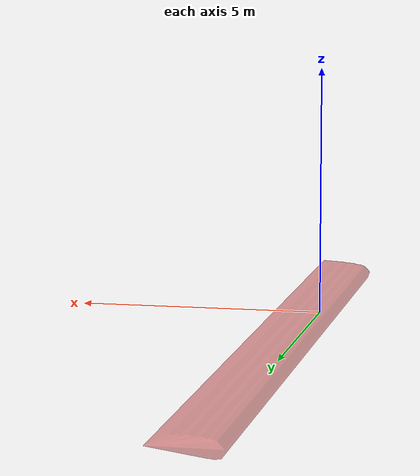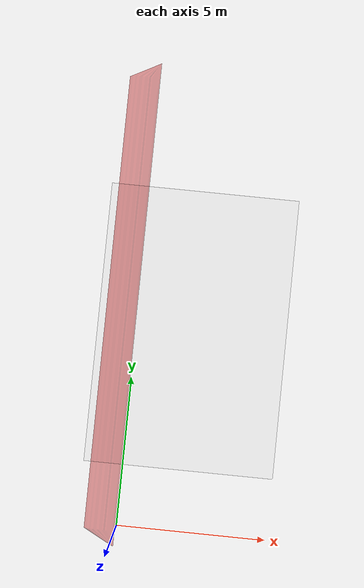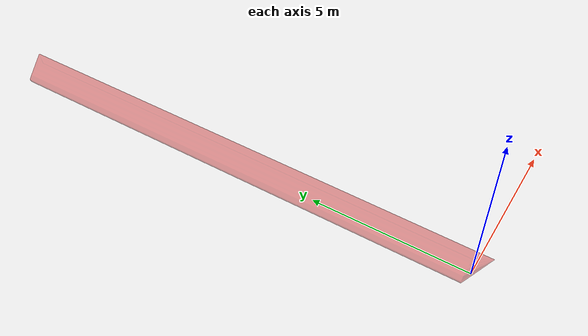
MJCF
<mujoco>
    <option density="1.2" viscosity="2e-05" wind="0 0 0"/>
    <worldbody>
        <light name="top" pos="0 0 5"/>
        <!-- Body -->

    <body name="body" pos="0 0 1" euler="90 180 -20">
        <freejoint/>
        <!-- Main Wing -->
        <geom name="vehicle-wing"  density="1.67" rgba="0.8 0.2 0.2 0.5" type="mesh" mesh="vehicle-wing-mesh"/>
        <camera name="fixed" pos="-100 -100 -10" xyaxes="1 0 0 0 1 2"/>
        <camera name="track" pos="0 0 0" xyaxes="1 2 0 0 1 2" mode="track"/>
    </body>

        <!-- Landing Platform -->
        <body name="platform" pos="0 0 0">
            <geom name="platform-geom" type="box" size="1500 1500 1" rgba="1 1 1 1" pos="0 0 -80"/>
        </body>
    </worldbody>

            <asset>
                <mesh name="vehicle-wing-mesh" vertex="0.0 0.0 0.0 0.045454545454545456 0.022727272727272728 0.0 0.09090909090909091 0.022727272727272728 0.0 0.13636363636363635 0.045454545454545456 0.0 0.18181818181818182 0.045454545454545456 0.0 0.2272727272727273 0.045454545454545456 0.0 0.2727272727272727 0.045454545454545456 0.0 0.3181818181818182 0.06818181818181818 0.0 0.36363636363636365 0.06818181818181818 0.0 0.4090909090909091 0.09090909090909091 0.0 0.4545454545454546 0.09090909090909091 0.0 0.5 0.09090909090909091 0.0 0.5454545454545454 0.06818181818181818 0.0 0.5909090909090909 0.06818181818181818 0.0 0.6363636363636364 0.06818181818181818 0.0 0.6818181818181819 0.06818181818181818 0.0 0.7272727272727273 0.045454545454545456 0.0 0.7727272727272727 0.045454545454545456 0.0 0.8181818181818182 0.022727272727272728 0.0 0.8636363636363636 0.045454545454545456 0.0 0.9090909090909092 0.045454545454545456 0.0 0.9545454545454546 0.06818181818181818 0.0 1.0 0.09090909090909091 0.0 1.0 0.13636363636363635 0.0 1.0 0.18181818181818182 0.0 1.0 0.2272727272727273 0.0 0.9545454545454546 0.25 0.0 0.9090909090909092 0.2727272727272727 0.0 0.8636363636363636 0.29545454545454547 0.0 0.8181818181818182 0.29545454545454547 0.0 0.7727272727272727 0.29545454545454547 0.0 0.7272727272727273 0.2727272727272727 0.0 0.6818181818181819 0.2727272727272727 0.0 0.6363636363636364 0.2727272727272727 0.0 0.5909090909090909 0.25 0.0 0.5454545454545454 0.2272727272727273 0.0 0.5 0.2272727272727273 0.0 0.4545454545454546 0.2272727272727273 0.0 0.4090909090909091 0.20454545454545456 0.0 0.36363636363636365 0.18181818181818182 0.0 0.3181818181818182 0.18181818181818182 0.0 0.2727272727272727 0.13636363636363635 0.0 0.2272727272727273 0.13636363636363635 0.0 0.18181818181818182 0.11363636363636365 0.0 0.13636363636363635 0.09090909090909091 0.0 0.09090909090909091 0.06818181818181818 0.0 0.045454545454545456 0.045454545454545456 0.0 0.0 0.0 0.5 0.045454545454545456 0.022727272727272728 0.5 0.09090909090909091 0.022727272727272728 0.5 0.13636363636363635 0.045454545454545456 0.5 0.18181818181818182 0.045454545454545456 0.5 0.2272727272727273 0.045454545454545456 0.5 0.2727272727272727 0.045454545454545456 0.5 0.3181818181818182 0.06818181818181818 0.5 0.36363636363636365 0.06818181818181818 0.5 0.4090909090909091 0.09090909090909091 0.5 0.4545454545454546 0.09090909090909091 0.5 0.5 0.09090909090909091 0.5 0.5454545454545454 0.06818181818181818 0.5 0.5909090909090909 0.06818181818181818 0.5 0.6363636363636364 0.06818181818181818 0.5 0.6818181818181819 0.06818181818181818 0.5 0.7272727272727273 0.045454545454545456 0.5 0.7727272727272727 0.045454545454545456 0.5 0.8181818181818182 0.022727272727272728 0.5 0.8636363636363636 0.045454545454545456 0.5 0.9090909090909092 0.045454545454545456 0.5 0.9545454545454546 0.06818181818181818 0.5 1.0 0.09090909090909091 0.5 1.0 0.13636363636363635 0.5 1.0 0.18181818181818182 0.5 1.0 0.2272727272727273 0.5 0.9545454545454546 0.25 0.5 0.9090909090909092 0.2727272727272727 0.5 0.8636363636363636 0.29545454545454547 0.5 0.8181818181818182 0.29545454545454547 0.5 0.7727272727272727 0.29545454545454547 0.5 0.7272727272727273 0.2727272727272727 0.5 0.6818181818181819 0.2727272727272727 0.5 0.6363636363636364 0.2727272727272727 0.5 0.5909090909090909 0.25 0.5 0.5454545454545454 0.2272727272727273 0.5 0.5 0.2272727272727273 0.5 0.4545454545454546 0.2272727272727273 0.5 0.4090909090909091 0.20454545454545456 0.5 0.36363636363636365 0.18181818181818182 0.5 0.3181818181818182 0.18181818181818182 0.5 0.2727272727272727 0.13636363636363635 0.5 0.2272727272727273 0.13636363636363635 0.5 0.18181818181818182 0.11363636363636365 0.5 0.13636363636363635 0.09090909090909091 0.5 0.09090909090909091 0.06818181818181818 0.5 0.045454545454545456 0.045454545454545456 0.5 0.0 0.0 1.0 0.045454545454545456 0.022727272727272728 1.0 0.09090909090909091 0.022727272727272728 1.0 0.13636363636363635 0.045454545454545456 1.0 0.18181818181818182 0.045454545454545456 1.0 0.2272727272727273 0.045454545454545456 1.0 0.2727272727272727 0.045454545454545456 1.0 0.3181818181818182 0.06818181818181818 1.0 0.36363636363636365 0.06818181818181818 1.0 0.4090909090909091 0.09090909090909091 1.0 0.4545454545454546 0.09090909090909091 1.0 0.5 0.09090909090909091 1.0 0.5454545454545454 0.06818181818181818 1.0 0.5909090909090909 0.06818181818181818 1.0 0.6363636363636364 0.06818181818181818 1.0 0.6818181818181819 0.06818181818181818 1.0 0.7272727272727273 0.045454545454545456 1.0 0.7727272727272727 0.045454545454545456 1.0 0.8181818181818182 0.022727272727272728 1.0 0.8636363636363636 0.045454545454545456 1.0 0.9090909090909092 0.045454545454545456 1.0 0.9545454545454546 0.06818181818181818 1.0 1.0 0.09090909090909091 1.0 1.0 0.13636363636363635 1.0 1.0 0.18181818181818182 1.0 1.0 0.2272727272727273 1.0 0.9545454545454546 0.25 1.0 0.9090909090909092 0.2727272727272727 1.0 0.8636363636363636 0.29545454545454547 1.0 0.8181818181818182 0.29545454545454547 1.0 0.7727272727272727 0.29545454545454547 1.0 0.7272727272727273 0.2727272727272727 1.0 0.6818181818181819 0.2727272727272727 1.0 0.6363636363636364 0.2727272727272727 1.0 0.5909090909090909 0.25 1.0 0.5454545454545454 0.2272727272727273 1.0 0.5 0.2272727272727273 1.0 0.4545454545454546 0.2272727272727273 1.0 0.4090909090909091 0.20454545454545456 1.0 0.36363636363636365 0.18181818181818182 1.0 0.3181818181818182 0.18181818181818182 1.0 0.2727272727272727 0.13636363636363635 1.0 0.2272727272727273 0.13636363636363635 1.0 0.18181818181818182 0.11363636363636365 1.0 0.13636363636363635 0.09090909090909091 1.0 0.09090909090909091 0.06818181818181818 1.0 0.045454545454545456 0.045454545454545456 1.0 0.0 0.0 1.5 0.045454545454545456 0.022727272727272728 1.5 0.09090909090909091 0.022727272727272728 1.5 0.13636363636363635 0.045454545454545456 1.5 0.18181818181818182 0.045454545454545456 1.5 0.2272727272727273 0.045454545454545456 1.5 0.2727272727272727 0.045454545454545456 1.5 0.3181818181818182 0.06818181818181818 1.5 0.36363636363636365 0.06818181818181818 1.5 0.4090909090909091 0.09090909090909091 1.5 0.4545454545454546 0.09090909090909091 1.5 0.5 0.09090909090909091 1.5 0.5454545454545454 0.06818181818181818 1.5 0.5909090909090909 0.06818181818181818 1.5 0.6363636363636364 0.06818181818181818 1.5 0.6818181818181819 0.06818181818181818 1.5 0.7272727272727273 0.045454545454545456 1.5 0.7727272727272727 0.045454545454545456 1.5 0.8181818181818182 0.022727272727272728 1.5 0.8636363636363636 0.045454545454545456 1.5 0.9090909090909092 0.045454545454545456 1.5 0.9545454545454546 0.06818181818181818 1.5 1.0 0.09090909090909091 1.5 1.0 0.13636363636363635 1.5 1.0 0.18181818181818182 1.5 1.0 0.2272727272727273 1.5 0.9545454545454546 0.25 1.5 0.9090909090909092 0.2727272727272727 1.5 0.8636363636363636 0.29545454545454547 1.5 0.8181818181818182 0.29545454545454547 1.5 0.7727272727272727 0.29545454545454547 1.5 0.7272727272727273 0.2727272727272727 1.5 0.6818181818181819 0.2727272727272727 1.5 0.6363636363636364 0.2727272727272727 1.5 0.5909090909090909 0.25 1.5 0.5454545454545454 0.2272727272727273 1.5 0.5 0.2272727272727273 1.5 0.4545454545454546 0.2272727272727273 1.5 0.4090909090909091 0.20454545454545456 1.5 0.36363636363636365 0.18181818181818182 1.5 0.3181818181818182 0.18181818181818182 1.5 0.2727272727272727 0.13636363636363635 1.5 0.2272727272727273 0.13636363636363635 1.5 0.18181818181818182 0.11363636363636365 1.5 0.13636363636363635 0.09090909090909091 1.5 0.09090909090909091 0.06818181818181818 1.5 0.045454545454545456 0.045454545454545456 1.5 0.0 0.0 2.0 0.045454545454545456 0.022727272727272728 2.0 0.09090909090909091 0.022727272727272728 2.0 0.13636363636363635 0.045454545454545456 2.0 0.18181818181818182 0.045454545454545456 2.0 0.2272727272727273 0.045454545454545456 2.0 0.2727272727272727 0.045454545454545456 2.0 0.3181818181818182 0.06818181818181818 2.0 0.36363636363636365 0.06818181818181818 2.0 0.4090909090909091 0.09090909090909091 2.0 0.4545454545454546 0.09090909090909091 2.0 0.5 0.09090909090909091 2.0 0.5454545454545454 0.06818181818181818 2.0 0.5909090909090909 0.06818181818181818 2.0 0.6363636363636364 0.06818181818181818 2.0 0.6818181818181819 0.06818181818181818 2.0 0.7272727272727273 0.045454545454545456 2.0 0.7727272727272727 0.045454545454545456 2.0 0.8181818181818182 0.022727272727272728 2.0 0.8636363636363636 0.045454545454545456 2.0 0.9090909090909092 0.045454545454545456 2.0 0.9545454545454546 0.06818181818181818 2.0 1.0 0.09090909090909091 2.0 1.0 0.13636363636363635 2.0 1.0 0.18181818181818182 2.0 1.0 0.2272727272727273 2.0 0.9545454545454546 0.25 2.0 0.9090909090909092 0.2727272727272727 2.0 0.8636363636363636 0.29545454545454547 2.0 0.8181818181818182 0.29545454545454547 2.0 0.7727272727272727 0.29545454545454547 2.0 0.7272727272727273 0.2727272727272727 2.0 0.6818181818181819 0.2727272727272727 2.0 0.6363636363636364 0.2727272727272727 2.0 0.5909090909090909 0.25 2.0 0.5454545454545454 0.2272727272727273 2.0 0.5 0.2272727272727273 2.0 0.4545454545454546 0.2272727272727273 2.0 0.4090909090909091 0.20454545454545456 2.0 0.36363636363636365 0.18181818181818182 2.0 0.3181818181818182 0.18181818181818182 2.0 0.2727272727272727 0.13636363636363635 2.0 0.2272727272727273 0.13636363636363635 2.0 0.18181818181818182 0.11363636363636365 2.0 0.13636363636363635 0.09090909090909091 2.0 0.09090909090909091 0.06818181818181818 2.0 0.045454545454545456 0.045454545454545456 2.0 0.0 0.0 2.5 0.045454545454545456 0.022727272727272728 2.5 0.09090909090909091 0.022727272727272728 2.5 0.13636363636363635 0.045454545454545456 2.5 0.18181818181818182 0.045454545454545456 2.5 0.2272727272727273 0.045454545454545456 2.5 0.2727272727272727 0.045454545454545456 2.5 0.3181818181818182 0.06818181818181818 2.5 0.36363636363636365 0.06818181818181818 2.5 0.4090909090909091 0.09090909090909091 2.5 0.4545454545454546 0.09090909090909091 2.5 0.5 0.09090909090909091 2.5 0.5454545454545454 0.06818181818181818 2.5 0.5909090909090909 0.06818181818181818 2.5 0.6363636363636364 0.06818181818181818 2.5 0.6818181818181819 0.06818181818181818 2.5 0.7272727272727273 0.045454545454545456 2.5 0.7727272727272727 0.045454545454545456 2.5 0.8181818181818182 0.022727272727272728 2.5 0.8636363636363636 0.045454545454545456 2.5 0.9090909090909092 0.045454545454545456 2.5 0.9545454545454546 0.06818181818181818 2.5 1.0 0.09090909090909091 2.5 1.0 0.13636363636363635 2.5 1.0 0.18181818181818182 2.5 1.0 0.2272727272727273 2.5 0.9545454545454546 0.25 2.5 0.9090909090909092 0.2727272727272727 2.5 0.8636363636363636 0.29545454545454547 2.5 0.8181818181818182 0.29545454545454547 2.5 0.7727272727272727 0.29545454545454547 2.5 0.7272727272727273 0.2727272727272727 2.5 0.6818181818181819 0.2727272727272727 2.5 0.6363636363636364 0.2727272727272727 2.5 0.5909090909090909 0.25 2.5 0.5454545454545454 0.2272727272727273 2.5 0.5 0.2272727272727273 2.5 0.4545454545454546 0.2272727272727273 2.5 0.4090909090909091 0.20454545454545456 2.5 0.36363636363636365 0.18181818181818182 2.5 0.3181818181818182 0.18181818181818182 2.5 0.2727272727272727 0.13636363636363635 2.5 0.2272727272727273 0.13636363636363635 2.5 0.18181818181818182 0.11363636363636365 2.5 0.13636363636363635 0.09090909090909091 2.5 0.09090909090909091 0.06818181818181818 2.5 0.045454545454545456 0.045454545454545456 2.5 0.0 0.0 3.0 0.045454545454545456 0.022727272727272728 3.0 0.09090909090909091 0.022727272727272728 3.0 0.13636363636363635 0.045454545454545456 3.0 0.18181818181818182 0.045454545454545456 3.0 0.2272727272727273 0.045454545454545456 3.0 0.2727272727272727 0.045454545454545456 3.0 0.3181818181818182 0.06818181818181818 3.0 0.36363636363636365 0.06818181818181818 3.0 0.4090909090909091 0.09090909090909091 3.0 0.4545454545454546 0.09090909090909091 3.0 0.5 0.09090909090909091 3.0 0.5454545454545454 0.06818181818181818 3.0 0.5909090909090909 0.06818181818181818 3.0 0.6363636363636364 0.06818181818181818 3.0 0.6818181818181819 0.06818181818181818 3.0 0.7272727272727273 0.045454545454545456 3.0 0.7727272727272727 0.045454545454545456 3.0 0.8181818181818182 0.022727272727272728 3.0 0.8636363636363636 0.045454545454545456 3.0 0.9090909090909092 0.045454545454545456 3.0 0.9545454545454546 0.06818181818181818 3.0 1.0 0.09090909090909091 3.0 1.0 0.13636363636363635 3.0 1.0 0.18181818181818182 3.0 1.0 0.2272727272727273 3.0 0.9545454545454546 0.25 3.0 0.9090909090909092 0.2727272727272727 3.0 0.8636363636363636 0.29545454545454547 3.0 0.8181818181818182 0.29545454545454547 3.0 0.7727272727272727 0.29545454545454547 3.0 0.7272727272727273 0.2727272727272727 3.0 0.6818181818181819 0.2727272727272727 3.0 0.6363636363636364 0.2727272727272727 3.0 0.5909090909090909 0.25 3.0 0.5454545454545454 0.2272727272727273 3.0 0.5 0.2272727272727273 3.0 0.4545454545454546 0.2272727272727273 3.0 0.4090909090909091 0.20454545454545456 3.0 0.36363636363636365 0.18181818181818182 3.0 0.3181818181818182 0.18181818181818182 3.0 0.2727272727272727 0.13636363636363635 3.0 0.2272727272727273 0.13636363636363635 3.0 0.18181818181818182 0.11363636363636365 3.0 0.13636363636363635 0.09090909090909091 3.0 0.09090909090909091 0.06818181818181818 3.0 0.045454545454545456 0.045454545454545456 3.0 0.0 0.0 3.5 0.045454545454545456 0.022727272727272728 3.5 0.09090909090909091 0.022727272727272728 3.5 0.13636363636363635 0.045454545454545456 3.5 0.18181818181818182 0.045454545454545456 3.5 0.2272727272727273 0.045454545454545456 3.5 0.2727272727272727 0.045454545454545456 3.5 0.3181818181818182 0.06818181818181818 3.5 0.36363636363636365 0.06818181818181818 3.5 0.4090909090909091 0.09090909090909091 3.5 0.4545454545454546 0.09090909090909091 3.5 0.5 0.09090909090909091 3.5 0.5454545454545454 0.06818181818181818 3.5 0.5909090909090909 0.06818181818181818 3.5 0.6363636363636364 0.06818181818181818 3.5 0.6818181818181819 0.06818181818181818 3.5 0.7272727272727273 0.045454545454545456 3.5 0.7727272727272727 0.045454545454545456 3.5 0.8181818181818182 0.022727272727272728 3.5 0.8636363636363636 0.045454545454545456 3.5 0.9090909090909092 0.045454545454545456 3.5 0.9545454545454546 0.06818181818181818 3.5 1.0 0.09090909090909091 3.5 1.0 0.13636363636363635 3.5 1.0 0.18181818181818182 3.5 1.0 0.2272727272727273 3.5 0.9545454545454546 0.25 3.5 0.9090909090909092 0.2727272727272727 3.5 0.8636363636363636 0.29545454545454547 3.5 0.8181818181818182 0.29545454545454547 3.5 0.7727272727272727 0.29545454545454547 3.5 0.7272727272727273 0.2727272727272727 3.5 0.6818181818181819 0.2727272727272727 3.5 0.6363636363636364 0.2727272727272727 3.5 0.5909090909090909 0.25 3.5 0.5454545454545454 0.2272727272727273 3.5 0.5 0.2272727272727273 3.5 0.4545454545454546 0.2272727272727273 3.5 0.4090909090909091 0.20454545454545456 3.5 0.36363636363636365 0.18181818181818182 3.5 0.3181818181818182 0.18181818181818182 3.5 0.2727272727272727 0.13636363636363635 3.5 0.2272727272727273 0.13636363636363635 3.5 0.18181818181818182 0.11363636363636365 3.5 0.13636363636363635 0.09090909090909091 3.5 0.09090909090909091 0.06818181818181818 3.5 0.045454545454545456 0.045454545454545456 3.5 0.0 0.0 4.0 0.045454545454545456 0.022727272727272728 4.0 0.09090909090909091 0.022727272727272728 4.0 0.13636363636363635 0.045454545454545456 4.0 0.18181818181818182 0.045454545454545456 4.0 0.2272727272727273 0.045454545454545456 4.0 0.2727272727272727 0.045454545454545456 4.0 0.3181818181818182 0.06818181818181818 4.0 0.36363636363636365 0.06818181818181818 4.0 0.4090909090909091 0.09090909090909091 4.0 0.4545454545454546 0.09090909090909091 4.0 0.5 0.09090909090909091 4.0 0.5454545454545454 0.06818181818181818 4.0 0.5909090909090909 0.06818181818181818 4.0 0.6363636363636364 0.06818181818181818 4.0 0.6818181818181819 0.06818181818181818 4.0 0.7272727272727273 0.045454545454545456 4.0 0.7727272727272727 0.045454545454545456 4.0 0.8181818181818182 0.022727272727272728 4.0 0.8636363636363636 0.045454545454545456 4.0 0.9090909090909092 0.045454545454545456 4.0 0.9545454545454546 0.06818181818181818 4.0 1.0 0.09090909090909091 4.0 1.0 0.13636363636363635 4.0 1.0 0.18181818181818182 4.0 1.0 0.2272727272727273 4.0 0.9545454545454546 0.25 4.0 0.9090909090909092 0.2727272727272727 4.0 0.8636363636363636 0.29545454545454547 4.0 0.8181818181818182 0.29545454545454547 4.0 0.7727272727272727 0.29545454545454547 4.0 0.7272727272727273 0.2727272727272727 4.0 0.6818181818181819 0.2727272727272727 4.0 0.6363636363636364 0.2727272727272727 4.0 0.5909090909090909 0.25 4.0 0.5454545454545454 0.2272727272727273 4.0 0.5 0.2272727272727273 4.0 0.4545454545454546 0.2272727272727273 4.0 0.4090909090909091 0.20454545454545456 4.0 0.36363636363636365 0.18181818181818182 4.0 0.3181818181818182 0.18181818181818182 4.0 0.2727272727272727 0.13636363636363635 4.0 0.2272727272727273 0.13636363636363635 4.0 0.18181818181818182 0.11363636363636365 4.0 0.13636363636363635 0.09090909090909091 4.0 0.09090909090909091 0.06818181818181818 4.0 0.045454545454545456 0.045454545454545456 4.0 0.0 0.0 4.5 0.045454545454545456 0.022727272727272728 4.5 0.09090909090909091 0.022727272727272728 4.5 0.13636363636363635 0.045454545454545456 4.5 0.18181818181818182 0.045454545454545456 4.5 0.2272727272727273 0.045454545454545456 4.5 0.2727272727272727 0.045454545454545456 4.5 0.3181818181818182 0.06818181818181818 4.5 0.36363636363636365 0.06818181818181818 4.5 0.4090909090909091 0.09090909090909091 4.5 0.4545454545454546 0.09090909090909091 4.5 0.5 0.09090909090909091 4.5 0.5454545454545454 0.06818181818181818 4.5 0.5909090909090909 0.06818181818181818 4.5 0.6363636363636364 0.06818181818181818 4.5 0.6818181818181819 0.06818181818181818 4.5 0.7272727272727273 0.045454545454545456 4.5 0.7727272727272727 0.045454545454545456 4.5 0.8181818181818182 0.022727272727272728 4.5 0.8636363636363636 0.045454545454545456 4.5 0.9090909090909092 0.045454545454545456 4.5 0.9545454545454546 0.06818181818181818 4.5 1.0 0.09090909090909091 4.5 1.0 0.13636363636363635 4.5 1.0 0.18181818181818182 4.5 1.0 0.2272727272727273 4.5 0.9545454545454546 0.25 4.5 0.9090909090909092 0.2727272727272727 4.5 0.8636363636363636 0.29545454545454547 4.5 0.8181818181818182 0.29545454545454547 4.5 0.7727272727272727 0.29545454545454547 4.5 0.7272727272727273 0.2727272727272727 4.5 0.6818181818181819 0.2727272727272727 4.5 0.6363636363636364 0.2727272727272727 4.5 0.5909090909090909 0.25 4.5 0.5454545454545454 0.2272727272727273 4.5 0.5 0.2272727272727273 4.5 0.4545454545454546 0.2272727272727273 4.5 0.4090909090909091 0.20454545454545456 4.5 0.36363636363636365 0.18181818181818182 4.5 0.3181818181818182 0.18181818181818182 4.5 0.2727272727272727 0.13636363636363635 4.5 0.2272727272727273 0.13636363636363635 4.5 0.18181818181818182 0.11363636363636365 4.5 0.13636363636363635 0.09090909090909091 4.5 0.09090909090909091 0.06818181818181818 4.5 0.045454545454545456 0.045454545454545456 4.5 0.0 0.0 5.0 0.045454545454545456 0.022727272727272728 5.0 0.09090909090909091 0.022727272727272728 5.0 0.13636363636363635 0.045454545454545456 5.0 0.18181818181818182 0.045454545454545456 5.0 0.2272727272727273 0.045454545454545456 5.0 0.2727272727272727 0.045454545454545456 5.0 0.3181818181818182 0.06818181818181818 5.0 0.36363636363636365 0.06818181818181818 5.0 0.4090909090909091 0.09090909090909091 5.0 0.4545454545454546 0.09090909090909091 5.0 0.5 0.09090909090909091 5.0 0.5454545454545454 0.06818181818181818 5.0 0.5909090909090909 0.06818181818181818 5.0 0.6363636363636364 0.06818181818181818 5.0 0.6818181818181819 0.06818181818181818 5.0 0.7272727272727273 0.045454545454545456 5.0 0.7727272727272727 0.045454545454545456 5.0 0.8181818181818182 0.022727272727272728 5.0 0.8636363636363636 0.045454545454545456 5.0 0.9090909090909092 0.045454545454545456 5.0 0.9545454545454546 0.06818181818181818 5.0 1.0 0.09090909090909091 5.0 1.0 0.13636363636363635 5.0 1.0 0.18181818181818182 5.0 1.0 0.2272727272727273 5.0 0.9545454545454546 0.25 5.0 0.9090909090909092 0.2727272727272727 5.0 0.8636363636363636 0.29545454545454547 5.0 0.8181818181818182 0.29545454545454547 5.0 0.7727272727272727 0.29545454545454547 5.0 0.7272727272727273 0.2727272727272727 5.0 0.6818181818181819 0.2727272727272727 5.0 0.6363636363636364 0.2727272727272727 5.0 0.5909090909090909 0.25 5.0 0.5454545454545454 0.2272727272727273 5.0 0.5 0.2272727272727273 5.0 0.4545454545454546 0.2272727272727273 5.0 0.4090909090909091 0.20454545454545456 5.0 0.36363636363636365 0.18181818181818182 5.0 0.3181818181818182 0.18181818181818182 5.0 0.2727272727272727 0.13636363636363635 5.0 0.2272727272727273 0.13636363636363635 5.0 0.18181818181818182 0.11363636363636365 5.0 0.13636363636363635 0.09090909090909091 5.0 0.09090909090909091 0.06818181818181818 5.0 0.045454545454545456 0.045454545454545456 5.0 0.0 0.0 5.5 0.045454545454545456 0.022727272727272728 5.5 0.09090909090909091 0.022727272727272728 5.5 0.13636363636363635 0.045454545454545456 5.5 0.18181818181818182 0.045454545454545456 5.5 0.2272727272727273 0.045454545454545456 5.5 0.2727272727272727 0.045454545454545456 5.5 0.3181818181818182 0.06818181818181818 5.5 0.36363636363636365 0.06818181818181818 5.5 0.4090909090909091 0.09090909090909091 5.5 0.4545454545454546 0.09090909090909091 5.5 0.5 0.09090909090909091 5.5 0.5454545454545454 0.06818181818181818 5.5 0.5909090909090909 0.06818181818181818 5.5 0.6363636363636364 0.06818181818181818 5.5 0.6818181818181819 0.06818181818181818 5.5 0.7272727272727273 0.045454545454545456 5.5 0.7727272727272727 0.045454545454545456 5.5 0.8181818181818182 0.022727272727272728 5.5 0.8636363636363636 0.045454545454545456 5.5 0.9090909090909092 0.045454545454545456 5.5 0.9545454545454546 0.06818181818181818 5.5 1.0 0.09090909090909091 5.5 1.0 0.13636363636363635 5.5 1.0 0.18181818181818182 5.5 1.0 0.2272727272727273 5.5 0.9545454545454546 0.25 5.5 0.9090909090909092 0.2727272727272727 5.5 0.8636363636363636 0.29545454545454547 5.5 0.8181818181818182 0.29545454545454547 5.5 0.7727272727272727 0.29545454545454547 5.5 0.7272727272727273 0.2727272727272727 5.5 0.6818181818181819 0.2727272727272727 5.5 0.6363636363636364 0.2727272727272727 5.5 0.5909090909090909 0.25 5.5 0.5454545454545454 0.2272727272727273 5.5 0.5 0.2272727272727273 5.5 0.4545454545454546 0.2272727272727273 5.5 0.4090909090909091 0.20454545454545456 5.5 0.36363636363636365 0.18181818181818182 5.5 0.3181818181818182 0.18181818181818182 5.5 0.2727272727272727 0.13636363636363635 5.5 0.2272727272727273 0.13636363636363635 5.5 0.18181818181818182 0.11363636363636365 5.5 0.13636363636363635 0.09090909090909091 5.5 0.09090909090909091 0.06818181818181818 5.5 0.045454545454545456 0.045454545454545456 5.5 0.0 0.0 6.0 0.045454545454545456 0.022727272727272728 6.0 0.09090909090909091 0.022727272727272728 6.0 0.13636363636363635 0.045454545454545456 6.0 0.18181818181818182 0.045454545454545456 6.0 0.2272727272727273 0.045454545454545456 6.0 0.2727272727272727 0.045454545454545456 6.0 0.3181818181818182 0.06818181818181818 6.0 0.36363636363636365 0.06818181818181818 6.0 0.4090909090909091 0.09090909090909091 6.0 0.4545454545454546 0.09090909090909091 6.0 0.5 0.09090909090909091 6.0 0.5454545454545454 0.06818181818181818 6.0 0.5909090909090909 0.06818181818181818 6.0 0.6363636363636364 0.06818181818181818 6.0 0.6818181818181819 0.06818181818181818 6.0 0.7272727272727273 0.045454545454545456 6.0 0.7727272727272727 0.045454545454545456 6.0 0.8181818181818182 0.022727272727272728 6.0 0.8636363636363636 0.045454545454545456 6.0 0.9090909090909092 0.045454545454545456 6.0 0.9545454545454546 0.06818181818181818 6.0 1.0 0.09090909090909091 6.0 1.0 0.13636363636363635 6.0 1.0 0.18181818181818182 6.0 1.0 0.2272727272727273 6.0 0.9545454545454546 0.25 6.0 0.9090909090909092 0.2727272727272727 6.0 0.8636363636363636 0.29545454545454547 6.0 0.8181818181818182 0.29545454545454547 6.0 0.7727272727272727 0.29545454545454547 6.0 0.7272727272727273 0.2727272727272727 6.0 0.6818181818181819 0.2727272727272727 6.0 0.6363636363636364 0.2727272727272727 6.0 0.5909090909090909 0.25 6.0 0.5454545454545454 0.2272727272727273 6.0 0.5 0.2272727272727273 6.0 0.4545454545454546 0.2272727272727273 6.0 0.4090909090909091 0.20454545454545456 6.0 0.36363636363636365 0.18181818181818182 6.0 0.3181818181818182 0.18181818181818182 6.0 0.2727272727272727 0.13636363636363635 6.0 0.2272727272727273 0.13636363636363635 6.0 0.18181818181818182 0.11363636363636365 6.0 0.13636363636363635 0.09090909090909091 6.0 0.09090909090909091 0.06818181818181818 6.0 0.045454545454545456 0.045454545454545456 6.0 0.0 0.0 6.5 0.045454545454545456 0.022727272727272728 6.5 0.09090909090909091 0.022727272727272728 6.5 0.13636363636363635 0.045454545454545456 6.5 0.18181818181818182 0.045454545454545456 6.5 0.2272727272727273 0.045454545454545456 6.5 0.2727272727272727 0.045454545454545456 6.5 0.3181818181818182 0.06818181818181818 6.5 0.36363636363636365 0.06818181818181818 6.5 0.4090909090909091 0.09090909090909091 6.5 0.4545454545454546 0.09090909090909091 6.5 0.5 0.09090909090909091 6.5 0.5454545454545454 0.06818181818181818 6.5 0.5909090909090909 0.06818181818181818 6.5 0.6363636363636364 0.06818181818181818 6.5 0.6818181818181819 0.06818181818181818 6.5 0.7272727272727273 0.045454545454545456 6.5 0.7727272727272727 0.045454545454545456 6.5 0.8181818181818182 0.022727272727272728 6.5 0.8636363636363636 0.045454545454545456 6.5 0.9090909090909092 0.045454545454545456 6.5 0.9545454545454546 0.06818181818181818 6.5 1.0 0.09090909090909091 6.5 1.0 0.13636363636363635 6.5 1.0 0.18181818181818182 6.5 1.0 0.2272727272727273 6.5 0.9545454545454546 0.25 6.5 0.9090909090909092 0.2727272727272727 6.5 0.8636363636363636 0.29545454545454547 6.5 0.8181818181818182 0.29545454545454547 6.5 0.7727272727272727 0.29545454545454547 6.5 0.7272727272727273 0.2727272727272727 6.5 0.6818181818181819 0.2727272727272727 6.5 0.6363636363636364 0.2727272727272727 6.5 0.5909090909090909 0.25 6.5 0.5454545454545454 0.2272727272727273 6.5 0.5 0.2272727272727273 6.5 0.4545454545454546 0.2272727272727273 6.5 0.4090909090909091 0.20454545454545456 6.5 0.36363636363636365 0.18181818181818182 6.5 0.3181818181818182 0.18181818181818182 6.5 0.2727272727272727 0.13636363636363635 6.5 0.2272727272727273 0.13636363636363635 6.5 0.18181818181818182 0.11363636363636365 6.5 0.13636363636363635 0.09090909090909091 6.5 0.09090909090909091 0.06818181818181818 6.5 0.045454545454545456 0.045454545454545456 6.5 0.0 0.0 7.0 0.045454545454545456 0.022727272727272728 7.0 0.09090909090909091 0.022727272727272728 7.0 0.13636363636363635 0.045454545454545456 7.0 0.18181818181818182 0.045454545454545456 7.0 0.2272727272727273 0.045454545454545456 7.0 0.2727272727272727 0.045454545454545456 7.0 0.3181818181818182 0.06818181818181818 7.0 0.36363636363636365 0.06818181818181818 7.0 0.4090909090909091 0.09090909090909091 7.0 0.4545454545454546 0.09090909090909091 7.0 0.5 0.09090909090909091 7.0 0.5454545454545454 0.06818181818181818 7.0 0.5909090909090909 0.06818181818181818 7.0 0.6363636363636364 0.06818181818181818 7.0 0.6818181818181819 0.06818181818181818 7.0 0.7272727272727273 0.045454545454545456 7.0 0.7727272727272727 0.045454545454545456 7.0 0.8181818181818182 0.022727272727272728 7.0 0.8636363636363636 0.045454545454545456 7.0 0.9090909090909092 0.045454545454545456 7.0 0.9545454545454546 0.06818181818181818 7.0 1.0 0.09090909090909091 7.0 1.0 0.13636363636363635 7.0 1.0 0.18181818181818182 7.0 1.0 0.2272727272727273 7.0 0.9545454545454546 0.25 7.0 0.9090909090909092 0.2727272727272727 7.0 0.8636363636363636 0.29545454545454547 7.0 0.8181818181818182 0.29545454545454547 7.0 0.7727272727272727 0.29545454545454547 7.0 0.7272727272727273 0.2727272727272727 7.0 0.6818181818181819 0.2727272727272727 7.0 0.6363636363636364 0.2727272727272727 7.0 0.5909090909090909 0.25 7.0 0.5454545454545454 0.2272727272727273 7.0 0.5 0.2272727272727273 7.0 0.4545454545454546 0.2272727272727273 7.0 0.4090909090909091 0.20454545454545456 7.0 0.36363636363636365 0.18181818181818182 7.0 0.3181818181818182 0.18181818181818182 7.0 0.2727272727272727 0.13636363636363635 7.0 0.2272727272727273 0.13636363636363635 7.0 0.18181818181818182 0.11363636363636365 7.0 0.13636363636363635 0.09090909090909091 7.0 0.09090909090909091 0.06818181818181818 7.0 0.045454545454545456 0.045454545454545456 7.0 0.0 0.0 7.5 0.045454545454545456 0.022727272727272728 7.5 0.09090909090909091 0.022727272727272728 7.5 0.13636363636363635 0.045454545454545456 7.5 0.18181818181818182 0.045454545454545456 7.5 0.2272727272727273 0.045454545454545456 7.5 0.2727272727272727 0.045454545454545456 7.5 0.3181818181818182 0.06818181818181818 7.5 0.36363636363636365 0.06818181818181818 7.5 0.4090909090909091 0.09090909090909091 7.5 0.4545454545454546 0.09090909090909091 7.5 0.5 0.09090909090909091 7.5 0.5454545454545454 0.06818181818181818 7.5 0.5909090909090909 0.06818181818181818 7.5 0.6363636363636364 0.06818181818181818 7.5 0.6818181818181819 0.06818181818181818 7.5 0.7272727272727273 0.045454545454545456 7.5 0.7727272727272727 0.045454545454545456 7.5 0.8181818181818182 0.022727272727272728 7.5 0.8636363636363636 0.045454545454545456 7.5 0.9090909090909092 0.045454545454545456 7.5 0.9545454545454546 0.06818181818181818 7.5 1.0 0.09090909090909091 7.5 1.0 0.13636363636363635 7.5 1.0 0.18181818181818182 7.5 1.0 0.2272727272727273 7.5 0.9545454545454546 0.25 7.5 0.9090909090909092 0.2727272727272727 7.5 0.8636363636363636 0.29545454545454547 7.5 0.8181818181818182 0.29545454545454547 7.5 0.7727272727272727 0.29545454545454547 7.5 0.7272727272727273 0.2727272727272727 7.5 0.6818181818181819 0.2727272727272727 7.5 0.6363636363636364 0.2727272727272727 7.5 0.5909090909090909 0.25 7.5 0.5454545454545454 0.2272727272727273 7.5 0.5 0.2272727272727273 7.5 0.4545454545454546 0.2272727272727273 7.5 0.4090909090909091 0.20454545454545456 7.5 0.36363636363636365 0.18181818181818182 7.5 0.3181818181818182 0.18181818181818182 7.5 0.2727272727272727 0.13636363636363635 7.5 0.2272727272727273 0.13636363636363635 7.5 0.18181818181818182 0.11363636363636365 7.5 0.13636363636363635 0.09090909090909091 7.5 0.09090909090909091 0.06818181818181818 7.5 0.045454545454545456 0.045454545454545456 7.5 0.0 0.0 8.0 0.045454545454545456 0.022727272727272728 8.0 0.09090909090909091 0.022727272727272728 8.0 0.13636363636363635 0.045454545454545456 8.0 0.18181818181818182 0.045454545454545456 8.0 0.2272727272727273 0.045454545454545456 8.0 0.2727272727272727 0.045454545454545456 8.0 0.3181818181818182 0.06818181818181818 8.0 0.36363636363636365 0.06818181818181818 8.0 0.4090909090909091 0.09090909090909091 8.0 0.4545454545454546 0.09090909090909091 8.0 0.5 0.09090909090909091 8.0 0.5454545454545454 0.06818181818181818 8.0 0.5909090909090909 0.06818181818181818 8.0 0.6363636363636364 0.06818181818181818 8.0 0.6818181818181819 0.06818181818181818 8.0 0.7272727272727273 0.045454545454545456 8.0 0.7727272727272727 0.045454545454545456 8.0 0.8181818181818182 0.022727272727272728 8.0 0.8636363636363636 0.045454545454545456 8.0 0.9090909090909092 0.045454545454545456 8.0 0.9545454545454546 0.06818181818181818 8.0 1.0 0.09090909090909091 8.0 1.0 0.13636363636363635 8.0 1.0 0.18181818181818182 8.0 1.0 0.2272727272727273 8.0 0.9545454545454546 0.25 8.0 0.9090909090909092 0.2727272727272727 8.0 0.8636363636363636 0.29545454545454547 8.0 0.8181818181818182 0.29545454545454547 8.0 0.7727272727272727 0.29545454545454547 8.0 0.7272727272727273 0.2727272727272727 8.0 0.6818181818181819 0.2727272727272727 8.0 0.6363636363636364 0.2727272727272727 8.0 0.5909090909090909 0.25 8.0 0.5454545454545454 0.2272727272727273 8.0 0.5 0.2272727272727273 8.0 0.4545454545454546 0.2272727272727273 8.0 0.4090909090909091 0.20454545454545456 8.0 0.36363636363636365 0.18181818181818182 8.0 0.3181818181818182 0.18181818181818182 8.0 0.2727272727272727 0.13636363636363635 8.0 0.2272727272727273 0.13636363636363635 8.0 0.18181818181818182 0.11363636363636365 8.0 0.13636363636363635 0.09090909090909091 8.0 0.09090909090909091 0.06818181818181818 8.0 0.045454545454545456 0.045454545454545456 8.0 0.0 0.0 8.5 0.045454545454545456 0.022727272727272728 8.5 0.09090909090909091 0.022727272727272728 8.5 0.13636363636363635 0.045454545454545456 8.5 0.18181818181818182 0.045454545454545456 8.5 0.2272727272727273 0.045454545454545456 8.5 0.2727272727272727 0.045454545454545456 8.5 0.3181818181818182 0.06818181818181818 8.5 0.36363636363636365 0.06818181818181818 8.5 0.4090909090909091 0.09090909090909091 8.5 0.4545454545454546 0.09090909090909091 8.5 0.5 0.09090909090909091 8.5 0.5454545454545454 0.06818181818181818 8.5 0.5909090909090909 0.06818181818181818 8.5 0.6363636363636364 0.06818181818181818 8.5 0.6818181818181819 0.06818181818181818 8.5 0.7272727272727273 0.045454545454545456 8.5 0.7727272727272727 0.045454545454545456 8.5 0.8181818181818182 0.022727272727272728 8.5 0.8636363636363636 0.045454545454545456 8.5 0.9090909090909092 0.045454545454545456 8.5 0.9545454545454546 0.06818181818181818 8.5 1.0 0.09090909090909091 8.5 1.0 0.13636363636363635 8.5 1.0 0.18181818181818182 8.5 1.0 0.2272727272727273 8.5 0.9545454545454546 0.25 8.5 0.9090909090909092 0.2727272727272727 8.5 0.8636363636363636 0.29545454545454547 8.5 0.8181818181818182 0.29545454545454547 8.5 0.7727272727272727 0.29545454545454547 8.5 0.7272727272727273 0.2727272727272727 8.5 0.6818181818181819 0.2727272727272727 8.5 0.6363636363636364 0.2727272727272727 8.5 0.5909090909090909 0.25 8.5 0.5454545454545454 0.2272727272727273 8.5 0.5 0.2272727272727273 8.5 0.4545454545454546 0.2272727272727273 8.5 0.4090909090909091 0.20454545454545456 8.5 0.36363636363636365 0.18181818181818182 8.5 0.3181818181818182 0.18181818181818182 8.5 0.2727272727272727 0.13636363636363635 8.5 0.2272727272727273 0.13636363636363635 8.5 0.18181818181818182 0.11363636363636365 8.5 0.13636363636363635 0.09090909090909091 8.5 0.09090909090909091 0.06818181818181818 8.5 0.045454545454545456 0.045454545454545456 8.5 0.0 0.0 9.0 0.045454545454545456 0.022727272727272728 9.0 0.09090909090909091 0.022727272727272728 9.0 0.13636363636363635 0.045454545454545456 9.0 0.18181818181818182 0.045454545454545456 9.0 0.2272727272727273 0.045454545454545456 9.0 0.2727272727272727 0.045454545454545456 9.0 0.3181818181818182 0.06818181818181818 9.0 0.36363636363636365 0.06818181818181818 9.0 0.4090909090909091 0.09090909090909091 9.0 0.4545454545454546 0.09090909090909091 9.0 0.5 0.09090909090909091 9.0 0.5454545454545454 0.06818181818181818 9.0 0.5909090909090909 0.06818181818181818 9.0 0.6363636363636364 0.06818181818181818 9.0 0.6818181818181819 0.06818181818181818 9.0 0.7272727272727273 0.045454545454545456 9.0 0.7727272727272727 0.045454545454545456 9.0 0.8181818181818182 0.022727272727272728 9.0 0.8636363636363636 0.045454545454545456 9.0 0.9090909090909092 0.045454545454545456 9.0 0.9545454545454546 0.06818181818181818 9.0 1.0 0.09090909090909091 9.0 1.0 0.13636363636363635 9.0 1.0 0.18181818181818182 9.0 1.0 0.2272727272727273 9.0 0.9545454545454546 0.25 9.0 0.9090909090909092 0.2727272727272727 9.0 0.8636363636363636 0.29545454545454547 9.0 0.8181818181818182 0.29545454545454547 9.0 0.7727272727272727 0.29545454545454547 9.0 0.7272727272727273 0.2727272727272727 9.0 0.6818181818181819 0.2727272727272727 9.0 0.6363636363636364 0.2727272727272727 9.0 0.5909090909090909 0.25 9.0 0.5454545454545454 0.2272727272727273 9.0 0.5 0.2272727272727273 9.0 0.4545454545454546 0.2272727272727273 9.0 0.4090909090909091 0.20454545454545456 9.0 0.36363636363636365 0.18181818181818182 9.0 0.3181818181818182 0.18181818181818182 9.0 0.2727272727272727 0.13636363636363635 9.0 0.2272727272727273 0.13636363636363635 9.0 0.18181818181818182 0.11363636363636365 9.0 0.13636363636363635 0.09090909090909091 9.0 0.09090909090909091 0.06818181818181818 9.0 0.045454545454545456 0.045454545454545456 9.0 0.0 0.0 9.5 0.045454545454545456 0.022727272727272728 9.5 0.09090909090909091 0.022727272727272728 9.5 0.13636363636363635 0.045454545454545456 9.5 0.18181818181818182 0.045454545454545456 9.5 0.2272727272727273 0.045454545454545456 9.5 0.2727272727272727 0.045454545454545456 9.5 0.3181818181818182 0.06818181818181818 9.5 0.36363636363636365 0.06818181818181818 9.5 0.4090909090909091 0.09090909090909091 9.5 0.4545454545454546 0.09090909090909091 9.5 0.5 0.09090909090909091 9.5 0.5454545454545454 0.06818181818181818 9.5 0.5909090909090909 0.06818181818181818 9.5 0.6363636363636364 0.06818181818181818 9.5 0.6818181818181819 0.06818181818181818 9.5 0.7272727272727273 0.045454545454545456 9.5 0.7727272727272727 0.045454545454545456 9.5 0.8181818181818182 0.022727272727272728 9.5 0.8636363636363636 0.045454545454545456 9.5 0.9090909090909092 0.045454545454545456 9.5 0.9545454545454546 0.06818181818181818 9.5 1.0 0.09090909090909091 9.5 1.0 0.13636363636363635 9.5 1.0 0.18181818181818182 9.5 1.0 0.2272727272727273 9.5 0.9545454545454546 0.25 9.5 0.9090909090909092 0.2727272727272727 9.5 0.8636363636363636 0.29545454545454547 9.5 0.8181818181818182 0.29545454545454547 9.5 0.7727272727272727 0.29545454545454547 9.5 0.7272727272727273 0.2727272727272727 9.5 0.6818181818181819 0.2727272727272727 9.5 0.6363636363636364 0.2727272727272727 9.5 0.5909090909090909 0.25 9.5 0.5454545454545454 0.2272727272727273 9.5 0.5 0.2272727272727273 9.5 0.4545454545454546 0.2272727272727273 9.5 0.4090909090909091 0.20454545454545456 9.5 0.36363636363636365 0.18181818181818182 9.5 0.3181818181818182 0.18181818181818182 9.5 0.2727272727272727 0.13636363636363635 9.5 0.2272727272727273 0.13636363636363635 9.5 0.18181818181818182 0.11363636363636365 9.5 0.13636363636363635 0.09090909090909091 9.5 0.09090909090909091 0.06818181818181818 9.5 0.045454545454545456 0.045454545454545456 9.5 0.0 0.0 10.0 0.045454545454545456 0.022727272727272728 10.0 0.09090909090909091 0.022727272727272728 10.0 0.13636363636363635 0.045454545454545456 10.0 0.18181818181818182 0.045454545454545456 10.0 0.2272727272727273 0.045454545454545456 10.0 0.2727272727272727 0.045454545454545456 10.0 0.3181818181818182 0.06818181818181818 10.0 0.36363636363636365 0.06818181818181818 10.0 0.4090909090909091 0.09090909090909091 10.0 0.4545454545454546 0.09090909090909091 10.0 0.5 0.09090909090909091 10.0 0.5454545454545454 0.06818181818181818 10.0 0.5909090909090909 0.06818181818181818 10.0 0.6363636363636364 0.06818181818181818 10.0 0.6818181818181819 0.06818181818181818 10.0 0.7272727272727273 0.045454545454545456 10.0 0.7727272727272727 0.045454545454545456 10.0 0.8181818181818182 0.022727272727272728 10.0 0.8636363636363636 0.045454545454545456 10.0 0.9090909090909092 0.045454545454545456 10.0 0.9545454545454546 0.06818181818181818 10.0 1.0 0.09090909090909091 10.0 1.0 0.13636363636363635 10.0 1.0 0.18181818181818182 10.0 1.0 0.2272727272727273 10.0 0.9545454545454546 0.25 10.0 0.9090909090909092 0.2727272727272727 10.0 0.8636363636363636 0.29545454545454547 10.0 0.8181818181818182 0.29545454545454547 10.0 0.7727272727272727 0.29545454545454547 10.0 0.7272727272727273 0.2727272727272727 10.0 0.6818181818181819 0.2727272727272727 10.0 0.6363636363636364 0.2727272727272727 10.0 0.5909090909090909 0.25 10.0 0.5454545454545454 0.2272727272727273 10.0 0.5 0.2272727272727273 10.0 0.4545454545454546 0.2272727272727273 10.0 0.4090909090909091 0.20454545454545456 10.0 0.36363636363636365 0.18181818181818182 10.0 0.3181818181818182 0.18181818181818182 10.0 0.2727272727272727 0.13636363636363635 10.0 0.2272727272727273 0.13636363636363635 10.0 0.18181818181818182 0.11363636363636365 10.0 0.13636363636363635 0.09090909090909091 10.0 0.09090909090909091 0.06818181818181818 10.0 0.045454545454545456 0.045454545454545456 10.0 0.0 0.0 10.5 0.045454545454545456 0.022727272727272728 10.5 0.09090909090909091 0.022727272727272728 10.5 0.13636363636363635 0.045454545454545456 10.5 0.18181818181818182 0.045454545454545456 10.5 0.2272727272727273 0.045454545454545456 10.5 0.2727272727272727 0.045454545454545456 10.5 0.3181818181818182 0.06818181818181818 10.5 0.36363636363636365 0.06818181818181818 10.5 0.4090909090909091 0.09090909090909091 10.5 0.4545454545454546 0.09090909090909091 10.5 0.5 0.09090909090909091 10.5 0.5454545454545454 0.06818181818181818 10.5 0.5909090909090909 0.06818181818181818 10.5 0.6363636363636364 0.06818181818181818 10.5 0.6818181818181819 0.06818181818181818 10.5 0.7272727272727273 0.045454545454545456 10.5 0.7727272727272727 0.045454545454545456 10.5 0.8181818181818182 0.022727272727272728 10.5 0.8636363636363636 0.045454545454545456 10.5 0.9090909090909092 0.045454545454545456 10.5 0.9545454545454546 0.06818181818181818 10.5 1.0 0.09090909090909091 10.5 1.0 0.13636363636363635 10.5 1.0 0.18181818181818182 10.5 1.0 0.2272727272727273 10.5 0.9545454545454546 0.25 10.5 0.9090909090909092 0.2727272727272727 10.5 0.8636363636363636 0.29545454545454547 10.5 0.8181818181818182 0.29545454545454547 10.5 0.7727272727272727 0.29545454545454547 10.5 0.7272727272727273 0.2727272727272727 10.5 0.6818181818181819 0.2727272727272727 10.5 0.6363636363636364 0.2727272727272727 10.5 0.5909090909090909 0.25 10.5 0.5454545454545454 0.2272727272727273 10.5 0.5 0.2272727272727273 10.5 0.4545454545454546 0.2272727272727273 10.5 0.4090909090909091 0.20454545454545456 10.5 0.36363636363636365 0.18181818181818182 10.5 0.3181818181818182 0.18181818181818182 10.5 0.2727272727272727 0.13636363636363635 10.5 0.2272727272727273 0.13636363636363635 10.5 0.18181818181818182 0.11363636363636365 10.5 0.13636363636363635 0.09090909090909091 10.5 0.09090909090909091 0.06818181818181818 10.5 0.045454545454545456 0.045454545454545456 10.5 0.0 0.0 11.0 0.045454545454545456 0.022727272727272728 11.0 0.09090909090909091 0.022727272727272728 11.0 0.13636363636363635 0.045454545454545456 11.0 0.18181818181818182 0.045454545454545456 11.0 0.2272727272727273 0.045454545454545456 11.0 0.2727272727272727 0.045454545454545456 11.0 0.3181818181818182 0.06818181818181818 11.0 0.36363636363636365 0.06818181818181818 11.0 0.4090909090909091 0.09090909090909091 11.0 0.4545454545454546 0.09090909090909091 11.0 0.5 0.09090909090909091 11.0 0.5454545454545454 0.06818181818181818 11.0 0.5909090909090909 0.06818181818181818 11.0 0.6363636363636364 0.06818181818181818 11.0 0.6818181818181819 0.06818181818181818 11.0 0.7272727272727273 0.045454545454545456 11.0 0.7727272727272727 0.045454545454545456 11.0 0.8181818181818182 0.022727272727272728 11.0 0.8636363636363636 0.045454545454545456 11.0 0.9090909090909092 0.045454545454545456 11.0 0.9545454545454546 0.06818181818181818 11.0 1.0 0.09090909090909091 11.0 1.0 0.13636363636363635 11.0 1.0 0.18181818181818182 11.0 1.0 0.2272727272727273 11.0 0.9545454545454546 0.25 11.0 0.9090909090909092 0.2727272727272727 11.0 0.8636363636363636 0.29545454545454547 11.0 0.8181818181818182 0.29545454545454547 11.0 0.7727272727272727 0.29545454545454547 11.0 0.7272727272727273 0.2727272727272727 11.0 0.6818181818181819 0.2727272727272727 11.0 0.6363636363636364 0.2727272727272727 11.0 0.5909090909090909 0.25 11.0 0.5454545454545454 0.2272727272727273 11.0 0.5 0.2272727272727273 11.0 0.4545454545454546 0.2272727272727273 11.0 0.4090909090909091 0.20454545454545456 11.0 0.36363636363636365 0.18181818181818182 11.0 0.3181818181818182 0.18181818181818182 11.0 0.2727272727272727 0.13636363636363635 11.0 0.2272727272727273 0.13636363636363635 11.0 0.18181818181818182 0.11363636363636365 11.0 0.13636363636363635 0.09090909090909091 11.0 0.09090909090909091 0.06818181818181818 11.0 0.045454545454545456 0.045454545454545456 11.0 0.0 0.0 11.5 0.045454545454545456 0.022727272727272728 11.5 0.09090909090909091 0.022727272727272728 11.5 0.13636363636363635 0.045454545454545456 11.5 0.18181818181818182 0.045454545454545456 11.5 0.2272727272727273 0.045454545454545456 11.5 0.2727272727272727 0.045454545454545456 11.5 0.3181818181818182 0.06818181818181818 11.5 0.36363636363636365 0.06818181818181818 11.5 0.4090909090909091 0.09090909090909091 11.5 0.4545454545454546 0.09090909090909091 11.5 0.5 0.09090909090909091 11.5 0.5454545454545454 0.06818181818181818 11.5 0.5909090909090909 0.06818181818181818 11.5 0.6363636363636364 0.06818181818181818 11.5 0.6818181818181819 0.06818181818181818 11.5 0.7272727272727273 0.045454545454545456 11.5 0.7727272727272727 0.045454545454545456 11.5 0.8181818181818182 0.022727272727272728 11.5 0.8636363636363636 0.045454545454545456 11.5 0.9090909090909092 0.045454545454545456 11.5 0.9545454545454546 0.06818181818181818 11.5 1.0 0.09090909090909091 11.5 1.0 0.13636363636363635 11.5 1.0 0.18181818181818182 11.5 1.0 0.2272727272727273 11.5 0.9545454545454546 0.25 11.5 0.9090909090909092 0.2727272727272727 11.5 0.8636363636363636 0.29545454545454547 11.5 0.8181818181818182 0.29545454545454547 11.5 0.7727272727272727 0.29545454545454547 11.5 0.7272727272727273 0.2727272727272727 11.5 0.6818181818181819 0.2727272727272727 11.5 0.6363636363636364 0.2727272727272727 11.5 0.5909090909090909 0.25 11.5 0.5454545454545454 0.2272727272727273 11.5 0.5 0.2272727272727273 11.5 0.4545454545454546 0.2272727272727273 11.5 0.4090909090909091 0.20454545454545456 11.5 0.36363636363636365 0.18181818181818182 11.5 0.3181818181818182 0.18181818181818182 11.5 0.2727272727272727 0.13636363636363635 11.5 0.2272727272727273 0.13636363636363635 11.5 0.18181818181818182 0.11363636363636365 11.5 0.13636363636363635 0.09090909090909091 11.5 0.09090909090909091 0.06818181818181818 11.5 0.045454545454545456 0.045454545454545456 11.5 0.0 0.0 12.0 0.045454545454545456 0.022727272727272728 12.0 0.09090909090909091 0.022727272727272728 12.0 0.13636363636363635 0.045454545454545456 12.0 0.18181818181818182 0.045454545454545456 12.0 0.2272727272727273 0.045454545454545456 12.0 0.2727272727272727 0.045454545454545456 12.0 0.3181818181818182 0.06818181818181818 12.0 0.36363636363636365 0.06818181818181818 12.0 0.4090909090909091 0.09090909090909091 12.0 0.4545454545454546 0.09090909090909091 12.0 0.5 0.09090909090909091 12.0 0.5454545454545454 0.06818181818181818 12.0 0.5909090909090909 0.06818181818181818 12.0 0.6363636363636364 0.06818181818181818 12.0 0.6818181818181819 0.06818181818181818 12.0 0.7272727272727273 0.045454545454545456 12.0 0.7727272727272727 0.045454545454545456 12.0 0.8181818181818182 0.022727272727272728 12.0 0.8636363636363636 0.045454545454545456 12.0 0.9090909090909092 0.045454545454545456 12.0 0.9545454545454546 0.06818181818181818 12.0 1.0 0.09090909090909091 12.0 1.0 0.13636363636363635 12.0 1.0 0.18181818181818182 12.0 1.0 0.2272727272727273 12.0 0.9545454545454546 0.25 12.0 0.9090909090909092 0.2727272727272727 12.0 0.8636363636363636 0.29545454545454547 12.0 0.8181818181818182 0.29545454545454547 12.0 0.7727272727272727 0.29545454545454547 12.0 0.7272727272727273 0.2727272727272727 12.0 0.6818181818181819 0.2727272727272727 12.0 0.6363636363636364 0.2727272727272727 12.0 0.5909090909090909 0.25 12.0 0.5454545454545454 0.2272727272727273 12.0 0.5 0.2272727272727273 12.0 0.4545454545454546 0.2272727272727273 12.0 0.4090909090909091 0.20454545454545456 12.0 0.36363636363636365 0.18181818181818182 12.0 0.3181818181818182 0.18181818181818182 12.0 0.2727272727272727 0.13636363636363635 12.0 0.2272727272727273 0.13636363636363635 12.0 0.18181818181818182 0.11363636363636365 12.0 0.13636363636363635 0.09090909090909091 12.0 0.09090909090909091 0.06818181818181818 12.0 0.045454545454545456 0.045454545454545456 12.0 0.0 0.0 12.5 0.045454545454545456 0.022727272727272728 12.5 0.09090909090909091 0.022727272727272728 12.5 0.13636363636363635 0.045454545454545456 12.5 0.18181818181818182 0.045454545454545456 12.5 0.2272727272727273 0.045454545454545456 12.5 0.2727272727272727 0.045454545454545456 12.5 0.3181818181818182 0.06818181818181818 12.5 0.36363636363636365 0.06818181818181818 12.5 0.4090909090909091 0.09090909090909091 12.5 0.4545454545454546 0.09090909090909091 12.5 0.5 0.09090909090909091 12.5 0.5454545454545454 0.06818181818181818 12.5 0.5909090909090909 0.06818181818181818 12.5 0.6363636363636364 0.06818181818181818 12.5 0.6818181818181819 0.06818181818181818 12.5 0.7272727272727273 0.045454545454545456 12.5 0.7727272727272727 0.045454545454545456 12.5 0.8181818181818182 0.022727272727272728 12.5 0.8636363636363636 0.045454545454545456 12.5 0.9090909090909092 0.045454545454545456 12.5 0.9545454545454546 0.06818181818181818 12.5 1.0 0.09090909090909091 12.5 1.0 0.13636363636363635 12.5 1.0 0.18181818181818182 12.5 1.0 0.2272727272727273 12.5 0.9545454545454546 0.25 12.5 0.9090909090909092 0.2727272727272727 12.5 0.8636363636363636 0.29545454545454547 12.5 0.8181818181818182 0.29545454545454547 12.5 0.7727272727272727 0.29545454545454547 12.5 0.7272727272727273 0.2727272727272727 12.5 0.6818181818181819 0.2727272727272727 12.5 0.6363636363636364 0.2727272727272727 12.5 0.5909090909090909 0.25 12.5 0.5454545454545454 0.2272727272727273 12.5 0.5 0.2272727272727273 12.5 0.4545454545454546 0.2272727272727273 12.5 0.4090909090909091 0.20454545454545456 12.5 0.36363636363636365 0.18181818181818182 12.5 0.3181818181818182 0.18181818181818182 12.5 0.2727272727272727 0.13636363636363635 12.5 0.2272727272727273 0.13636363636363635 12.5 0.18181818181818182 0.11363636363636365 12.5 0.13636363636363635 0.09090909090909091 12.5 0.09090909090909091 0.06818181818181818 12.5 0.045454545454545456 0.045454545454545456 12.5 0.0 0.0 13.0 0.045454545454545456 0.022727272727272728 13.0 0.09090909090909091 0.022727272727272728 13.0 0.13636363636363635 0.045454545454545456 13.0 0.18181818181818182 0.045454545454545456 13.0 0.2272727272727273 0.045454545454545456 13.0 0.2727272727272727 0.045454545454545456 13.0 0.3181818181818182 0.06818181818181818 13.0 0.36363636363636365 0.06818181818181818 13.0 0.4090909090909091 0.09090909090909091 13.0 0.4545454545454546 0.09090909090909091 13.0 0.5 0.09090909090909091 13.0 0.5454545454545454 0.06818181818181818 13.0 0.5909090909090909 0.06818181818181818 13.0 0.6363636363636364 0.06818181818181818 13.0 0.6818181818181819 0.06818181818181818 13.0 0.7272727272727273 0.045454545454545456 13.0 0.7727272727272727 0.045454545454545456 13.0 0.8181818181818182 0.022727272727272728 13.0 0.8636363636363636 0.045454545454545456 13.0 0.9090909090909092 0.045454545454545456 13.0 0.9545454545454546 0.06818181818181818 13.0 1.0 0.09090909090909091 13.0 1.0 0.13636363636363635 13.0 1.0 0.18181818181818182 13.0 1.0 0.2272727272727273 13.0 0.9545454545454546 0.25 13.0 0.9090909090909092 0.2727272727272727 13.0 0.8636363636363636 0.29545454545454547 13.0 0.8181818181818182 0.29545454545454547 13.0 0.7727272727272727 0.29545454545454547 13.0 0.7272727272727273 0.2727272727272727 13.0 0.6818181818181819 0.2727272727272727 13.0 0.6363636363636364 0.2727272727272727 13.0 0.5909090909090909 0.25 13.0 0.5454545454545454 0.2272727272727273 13.0 0.5 0.2272727272727273 13.0 0.4545454545454546 0.2272727272727273 13.0 0.4090909090909091 0.20454545454545456 13.0 0.36363636363636365 0.18181818181818182 13.0 0.3181818181818182 0.18181818181818182 13.0 0.2727272727272727 0.13636363636363635 13.0 0.2272727272727273 0.13636363636363635 13.0 0.18181818181818182 0.11363636363636365 13.0 0.13636363636363635 0.09090909090909091 13.0 0.09090909090909091 0.06818181818181818 13.0 0.045454545454545456 0.045454545454545456 13.0 0.0 0.0 13.5 0.045454545454545456 0.022727272727272728 13.5 0.09090909090909091 0.022727272727272728 13.5 0.13636363636363635 0.045454545454545456 13.5 0.18181818181818182 0.045454545454545456 13.5 0.2272727272727273 0.045454545454545456 13.5 0.2727272727272727 0.045454545454545456 13.5 0.3181818181818182 0.06818181818181818 13.5 0.36363636363636365 0.06818181818181818 13.5 0.4090909090909091 0.09090909090909091 13.5 0.4545454545454546 0.09090909090909091 13.5 0.5 0.09090909090909091 13.5 0.5454545454545454 0.06818181818181818 13.5 0.5909090909090909 0.06818181818181818 13.5 0.6363636363636364 0.06818181818181818 13.5 0.6818181818181819 0.06818181818181818 13.5 0.7272727272727273 0.045454545454545456 13.5 0.7727272727272727 0.045454545454545456 13.5 0.8181818181818182 0.022727272727272728 13.5 0.8636363636363636 0.045454545454545456 13.5 0.9090909090909092 0.045454545454545456 13.5 0.9545454545454546 0.06818181818181818 13.5 1.0 0.09090909090909091 13.5 1.0 0.13636363636363635 13.5 1.0 0.18181818181818182 13.5 1.0 0.2272727272727273 13.5 0.9545454545454546 0.25 13.5 0.9090909090909092 0.2727272727272727 13.5 0.8636363636363636 0.29545454545454547 13.5 0.8181818181818182 0.29545454545454547 13.5 0.7727272727272727 0.29545454545454547 13.5 0.7272727272727273 0.2727272727272727 13.5 0.6818181818181819 0.2727272727272727 13.5 0.6363636363636364 0.2727272727272727 13.5 0.5909090909090909 0.25 13.5 0.5454545454545454 0.2272727272727273 13.5 0.5 0.2272727272727273 13.5 0.4545454545454546 0.2272727272727273 13.5 0.4090909090909091 0.20454545454545456 13.5 0.36363636363636365 0.18181818181818182 13.5 0.3181818181818182 0.18181818181818182 13.5 0.2727272727272727 0.13636363636363635 13.5 0.2272727272727273 0.13636363636363635 13.5 0.18181818181818182 0.11363636363636365 13.5 0.13636363636363635 0.09090909090909091 13.5 0.09090909090909091 0.06818181818181818 13.5 0.045454545454545456 0.045454545454545456 13.5 0.0 0.0 14.0 0.045454545454545456 0.022727272727272728 14.0 0.09090909090909091 0.022727272727272728 14.0 0.13636363636363635 0.045454545454545456 14.0 0.18181818181818182 0.045454545454545456 14.0 0.2272727272727273 0.045454545454545456 14.0 0.2727272727272727 0.045454545454545456 14.0 0.3181818181818182 0.06818181818181818 14.0 0.36363636363636365 0.06818181818181818 14.0 0.4090909090909091 0.09090909090909091 14.0 0.4545454545454546 0.09090909090909091 14.0 0.5 0.09090909090909091 14.0 0.5454545454545454 0.06818181818181818 14.0 0.5909090909090909 0.06818181818181818 14.0 0.6363636363636364 0.06818181818181818 14.0 0.6818181818181819 0.06818181818181818 14.0 0.7272727272727273 0.045454545454545456 14.0 0.7727272727272727 0.045454545454545456 14.0 0.8181818181818182 0.022727272727272728 14.0 0.8636363636363636 0.045454545454545456 14.0 0.9090909090909092 0.045454545454545456 14.0 0.9545454545454546 0.06818181818181818 14.0 1.0 0.09090909090909091 14.0 1.0 0.13636363636363635 14.0 1.0 0.18181818181818182 14.0 1.0 0.2272727272727273 14.0 0.9545454545454546 0.25 14.0 0.9090909090909092 0.2727272727272727 14.0 0.8636363636363636 0.29545454545454547 14.0 0.8181818181818182 0.29545454545454547 14.0 0.7727272727272727 0.29545454545454547 14.0 0.7272727272727273 0.2727272727272727 14.0 0.6818181818181819 0.2727272727272727 14.0 0.6363636363636364 0.2727272727272727 14.0 0.5909090909090909 0.25 14.0 0.5454545454545454 0.2272727272727273 14.0 0.5 0.2272727272727273 14.0 0.4545454545454546 0.2272727272727273 14.0 0.4090909090909091 0.20454545454545456 14.0 0.36363636363636365 0.18181818181818182 14.0 0.3181818181818182 0.18181818181818182 14.0 0.2727272727272727 0.13636363636363635 14.0 0.2272727272727273 0.13636363636363635 14.0 0.18181818181818182 0.11363636363636365 14.0 0.13636363636363635 0.09090909090909091 14.0 0.09090909090909091 0.06818181818181818 14.0 0.045454545454545456 0.045454545454545456 14.0 0.0 0.0 14.5 0.045454545454545456 0.022727272727272728 14.5 0.09090909090909091 0.022727272727272728 14.5 0.13636363636363635 0.045454545454545456 14.5 0.18181818181818182 0.045454545454545456 14.5 0.2272727272727273 0.045454545454545456 14.5 0.2727272727272727 0.045454545454545456 14.5 0.3181818181818182 0.06818181818181818 14.5 0.36363636363636365 0.06818181818181818 14.5 0.4090909090909091 0.09090909090909091 14.5 0.4545454545454546 0.09090909090909091 14.5 0.5 0.09090909090909091 14.5 0.5454545454545454 0.06818181818181818 14.5 0.5909090909090909 0.06818181818181818 14.5 0.6363636363636364 0.06818181818181818 14.5 0.6818181818181819 0.06818181818181818 14.5 0.7272727272727273 0.045454545454545456 14.5 0.7727272727272727 0.045454545454545456 14.5 0.8181818181818182 0.022727272727272728 14.5 0.8636363636363636 0.045454545454545456 14.5 0.9090909090909092 0.045454545454545456 14.5 0.9545454545454546 0.06818181818181818 14.5 1.0 0.09090909090909091 14.5 1.0 0.13636363636363635 14.5 1.0 0.18181818181818182 14.5 1.0 0.2272727272727273 14.5 0.9545454545454546 0.25 14.5 0.9090909090909092 0.2727272727272727 14.5 0.8636363636363636 0.29545454545454547 14.5 0.8181818181818182 0.29545454545454547 14.5 0.7727272727272727 0.29545454545454547 14.5 0.7272727272727273 0.2727272727272727 14.5 0.6818181818181819 0.2727272727272727 14.5 0.6363636363636364 0.2727272727272727 14.5 0.5909090909090909 0.25 14.5 0.5454545454545454 0.2272727272727273 14.5 0.5 0.2272727272727273 14.5 0.4545454545454546 0.2272727272727273 14.5 0.4090909090909091 0.20454545454545456 14.5 0.36363636363636365 0.18181818181818182 14.5 0.3181818181818182 0.18181818181818182 14.5 0.2727272727272727 0.13636363636363635 14.5 0.2272727272727273 0.13636363636363635 14.5 0.18181818181818182 0.11363636363636365 14.5 0.13636363636363635 0.09090909090909091 14.5 0.09090909090909091 0.06818181818181818 14.5 0.045454545454545456 0.045454545454545456 14.5 0.0 0.0 15.0 0.045454545454545456 0.022727272727272728 15.0 0.09090909090909091 0.022727272727272728 15.0 0.13636363636363635 0.045454545454545456 15.0 0.18181818181818182 0.045454545454545456 15.0 0.2272727272727273 0.045454545454545456 15.0 0.2727272727272727 0.045454545454545456 15.0 0.3181818181818182 0.06818181818181818 15.0 0.36363636363636365 0.06818181818181818 15.0 0.4090909090909091 0.09090909090909091 15.0 0.4545454545454546 0.09090909090909091 15.0 0.5 0.09090909090909091 15.0 0.5454545454545454 0.06818181818181818 15.0 0.5909090909090909 0.06818181818181818 15.0 0.6363636363636364 0.06818181818181818 15.0 0.6818181818181819 0.06818181818181818 15.0 0.7272727272727273 0.045454545454545456 15.0 0.7727272727272727 0.045454545454545456 15.0 0.8181818181818182 0.022727272727272728 15.0 0.8636363636363636 0.045454545454545456 15.0 0.9090909090909092 0.045454545454545456 15.0 0.9545454545454546 0.06818181818181818 15.0 1.0 0.09090909090909091 15.0 1.0 0.13636363636363635 15.0 1.0 0.18181818181818182 15.0 1.0 0.2272727272727273 15.0 0.9545454545454546 0.25 15.0 0.9090909090909092 0.2727272727272727 15.0 0.8636363636363636 0.29545454545454547 15.0 0.8181818181818182 0.29545454545454547 15.0 0.7727272727272727 0.29545454545454547 15.0 0.7272727272727273 0.2727272727272727 15.0 0.6818181818181819 0.2727272727272727 15.0 0.6363636363636364 0.2727272727272727 15.0 0.5909090909090909 0.25 15.0 0.5454545454545454 0.2272727272727273 15.0 0.5 0.2272727272727273 15.0 0.4545454545454546 0.2272727272727273 15.0 0.4090909090909091 0.20454545454545456 15.0 0.36363636363636365 0.18181818181818182 15.0 0.3181818181818182 0.18181818181818182 15.0 0.2727272727272727 0.13636363636363635 15.0 0.2272727272727273 0.13636363636363635 15.0 0.18181818181818182 0.11363636363636365 15.0 0.13636363636363635 0.09090909090909091 15.0 0.09090909090909091 0.06818181818181818 15.0 0.045454545454545456 0.045454545454545456 15.0 0.0 0.0 -0.5 0.0 0.0 15.5" face="0 48 1 0 47 48 1 49 2 1 48 49 2 50 3 2 49 50 3 51 4 3 50 51 4 52 5 4 51 52 5 53 6 5 52 53 6 54 7 6 53 54 7 55 8 7 54 55 8 56 9 8 55 56 9 57 10 9 56 57 10 58 11 10 57 58 11 59 12 11 58 59 12 60 13 12 59 60 13 61 14 13 60 61 14 62 15 14 61 62 15 63 16 15 62 63 16 64 17 16 63 64 17 65 18 17 64 65 18 66 19 18 65 66 19 67 20 19 66 67 20 68 21 20 67 68 21 69 22 21 68 69 22 70 23 22 69 70 23 71 24 23 70 71 24 72 25 24 71 72 25 73 26 25 72 73 26 74 27 26 73 74 27 75 28 27 74 75 28 76 29 28 75 76 29 77 30 29 76 77 30 78 31 30 77 78 31 79 32 31 78 79 32 80 33 32 79 80 33 81 34 33 80 81 34 82 35 34 81 82 35 83 36 35 82 83 36 84 37 36 83 84 37 85 38 37 84 85 38 86 39 38 85 86 39 87 40 39 86 87 40 88 41 40 87 88 41 89 42 41 88 89 42 90 43 42 89 90 43 91 44 43 90 91 44 92 45 44 91 92 45 93 46 45 92 93 46 94 47 46 93 94 47 95 48 47 94 95 48 96 49 48 95 96 49 97 50 49 96 97 50 98 51 50 97 98 51 99 52 51 98 99 52 100 53 52 99 100 53 101 54 53 100 101 54 102 55 54 101 102 55 103 56 55 102 103 56 104 57 56 103 104 57 105 58 57 104 105 58 106 59 58 105 106 59 107 60 59 106 107 60 108 61 60 107 108 61 109 62 61 108 109 62 110 63 62 109 110 63 111 64 63 110 111 64 112 65 64 111 112 65 113 66 65 112 113 66 114 67 66 113 114 67 115 68 67 114 115 68 116 69 68 115 116 69 117 70 69 116 117 70 118 71 70 117 118 71 119 72 71 118 119 72 120 73 72 119 120 73 121 74 73 120 121 74 122 75 74 121 122 75 123 76 75 122 123 76 124 77 76 123 124 77 125 78 77 124 125 78 126 79 78 125 126 79 127 80 79 126 127 80 128 81 80 127 128 81 129 82 81 128 129 82 130 83 82 129 130 83 131 84 83 130 131 84 132 85 84 131 132 85 133 86 85 132 133 86 134 87 86 133 134 87 135 88 87 134 135 88 136 89 88 135 136 89 137 90 89 136 137 90 138 91 90 137 138 91 139 92 91 138 139 92 140 93 92 139 140 93 141 94 93 140 141 94 142 95 94 141 142 95 143 96 95 142 143 96 144 97 96 143 144 97 145 98 97 144 145 98 146 99 98 145 146 99 147 100 99 146 147 100 148 101 100 147 148 101 149 102 101 148 149 102 150 103 102 149 150 103 151 104 103 150 151 104 152 105 104 151 152 105 153 106 105 152 153 106 154 107 106 153 154 107 155 108 107 154 155 108 156 109 108 155 156 109 157 110 109 156 157 110 158 111 110 157 158 111 159 112 111 158 159 112 160 113 112 159 160 113 161 114 113 160 161 114 162 115 114 161 162 115 163 116 115 162 163 116 164 117 116 163 164 117 165 118 117 164 165 118 166 119 118 165 166 119 167 120 119 166 167 120 168 121 120 167 168 121 169 122 121 168 169 122 170 123 122 169 170 123 171 124 123 170 171 124 172 125 124 171 172 125 173 126 125 172 173 126 174 127 126 173 174 127 175 128 127 174 175 128 176 129 128 175 176 129 177 130 129 176 177 130 178 131 130 177 178 131 179 132 131 178 179 132 180 133 132 179 180 133 181 134 133 180 181 134 182 135 134 181 182 135 183 136 135 182 183 136 184 137 136 183 184 137 185 138 137 184 185 138 186 139 138 185 186 139 187 140 139 186 187 140 188 141 140 187 188 141 189 142 141 188 189 142 190 143 142 189 190 143 191 144 143 190 191 144 192 145 144 191 192 145 193 146 145 192 193 146 194 147 146 193 194 147 195 148 147 194 195 148 196 149 148 195 196 149 197 150 149 196 197 150 198 151 150 197 198 151 199 152 151 198 199 152 200 153 152 199 200 153 201 154 153 200 201 154 202 155 154 201 202 155 203 156 155 202 203 156 204 157 156 203 204 157 205 158 157 204 205 158 206 159 158 205 206 159 207 160 159 206 207 160 208 161 160 207 208 161 209 162 161 208 209 162 210 163 162 209 210 163 211 164 163 210 211 164 212 165 164 211 212 165 213 166 165 212 213 166 214 167 166 213 214 167 215 168 167 214 215 168 216 169 168 215 216 169 217 170 169 216 217 170 218 171 170 217 218 171 219 172 171 218 219 172 220 173 172 219 220 173 221 174 173 220 221 174 222 175 174 221 222 175 223 176 175 222 223 176 224 177 176 223 224 177 225 178 177 224 225 178 226 179 178 225 226 179 227 180 179 226 227 180 228 181 180 227 228 181 229 182 181 228 229 182 230 183 182 229 230 183 231 184 183 230 231 184 232 185 184 231 232 185 233 186 185 232 233 186 234 187 186 233 234 187 235 188 187 234 235 188 236 189 188 235 236 189 237 190 189 236 237 190 238 191 190 237 238 191 239 192 191 238 239 192 240 193 192 239 240 193 241 194 193 240 241 194 242 195 194 241 242 195 243 196 195 242 243 196 244 197 196 243 244 197 245 198 197 244 245 198 246 199 198 245 246 199 247 200 199 246 247 200 248 201 200 247 248 201 249 202 201 248 249 202 250 203 202 249 250 203 251 204 203 250 251 204 252 205 204 251 252 205 253 206 205 252 253 206 254 207 206 253 254 207 255 208 207 254 255 208 256 209 208 255 256 209 257 210 209 256 257 210 258 211 210 257 258 211 259 212 211 258 259 212 260 213 212 259 260 213 261 214 213 260 261 214 262 215 214 261 262 215 263 216 215 262 263 216 264 217 216 263 264 217 265 218 217 264 265 218 266 219 218 265 266 219 267 220 219 266 267 220 268 221 220 267 268 221 269 222 221 268 269 222 270 223 222 269 270 223 271 224 223 270 271 224 272 225 224 271 272 225 273 226 225 272 273 226 274 227 226 273 274 227 275 228 227 274 275 228 276 229 228 275 276 229 277 230 229 276 277 230 278 231 230 277 278 231 279 232 231 278 279 232 280 233 232 279 280 233 281 234 233 280 281 234 282 235 234 281 282 235 283 236 235 282 283 236 284 237 236 283 284 237 285 238 237 284 285 238 286 239 238 285 286 239 287 240 239 286 287 240 288 241 240 287 288 241 289 242 241 288 289 242 290 243 242 289 290 243 291 244 243 290 291 244 292 245 244 291 292 245 293 246 245 292 293 246 294 247 246 293 294 247 295 248 247 294 295 248 296 249 248 295 296 249 297 250 249 296 297 250 298 251 250 297 298 251 299 252 251 298 299 252 300 253 252 299 300 253 301 254 253 300 301 254 302 255 254 301 302 255 303 256 255 302 303 256 304 257 256 303 304 257 305 258 257 304 305 258 306 259 258 305 306 259 307 260 259 306 307 260 308 261 260 307 308 261 309 262 261 308 309 262 310 263 262 309 310 263 311 264 263 310 311 264 312 265 264 311 312 265 313 266 265 312 313 266 314 267 266 313 314 267 315 268 267 314 315 268 316 269 268 315 316 269 317 270 269 316 317 270 318 271 270 317 318 271 319 272 271 318 319 272 320 273 272 319 320 273 321 274 273 320 321 274 322 275 274 321 322 275 323 276 275 322 323 276 324 277 276 323 324 277 325 278 277 324 325 278 326 279 278 325 326 279 327 280 279 326 327 280 328 281 280 327 328 281 329 282 281 328 329 282 330 283 282 329 330 283 331 284 283 330 331 284 332 285 284 331 332 285 333 286 285 332 333 286 334 287 286 333 334 287 335 288 287 334 335 288 336 289 288 335 336 289 337 290 289 336 337 290 338 291 290 337 338 291 339 292 291 338 339 292 340 293 292 339 340 293 341 294 293 340 341 294 342 295 294 341 342 295 343 296 295 342 343 296 344 297 296 343 344 297 345 298 297 344 345 298 346 299 298 345 346 299 347 300 299 346 347 300 348 301 300 347 348 301 349 302 301 348 349 302 350 303 302 349 350 303 351 304 303 350 351 304 352 305 304 351 352 305 353 306 305 352 353 306 354 307 306 353 354 307 355 308 307 354 355 308 356 309 308 355 356 309 357 310 309 356 357 310 358 311 310 357 358 311 359 312 311 358 359 312 360 313 312 359 360 313 361 314 313 360 361 314 362 315 314 361 362 315 363 316 315 362 363 316 364 317 316 363 364 317 365 318 317 364 365 318 366 319 318 365 366 319 367 320 319 366 367 320 368 321 320 367 368 321 369 322 321 368 369 322 370 323 322 369 370 323 371 324 323 370 371 324 372 325 324 371 372 325 373 326 325 372 373 326 374 327 326 373 374 327 375 328 327 374 375 328 376 329 328 375 376 329 377 330 329 376 377 330 378 331 330 377 378 331 379 332 331 378 379 332 380 333 332 379 380 333 381 334 333 380 381 334 382 335 334 381 382 335 383 336 335 382 383 336 384 337 336 383 384 337 385 338 337 384 385 338 386 339 338 385 386 339 387 340 339 386 387 340 388 341 340 387 388 341 389 342 341 388 389 342 390 343 342 389 390 343 391 344 343 390 391 344 392 345 344 391 392 345 393 346 345 392 393 346 394 347 346 393 394 347 395 348 347 394 395 348 396 349 348 395 396 349 397 350 349 396 397 350 398 351 350 397 398 351 399 352 351 398 399 352 400 353 352 399 400 353 401 354 353 400 401 354 402 355 354 401 402 355 403 356 355 402 403 356 404 357 356 403 404 357 405 358 357 404 405 358 406 359 358 405 406 359 407 360 359 406 407 360 408 361 360 407 408 361 409 362 361 408 409 362 410 363 362 409 410 363 411 364 363 410 411 364 412 365 364 411 412 365 413 366 365 412 413 366 414 367 366 413 414 367 415 368 367 414 415 368 416 369 368 415 416 369 417 370 369 416 417 370 418 371 370 417 418 371 419 372 371 418 419 372 420 373 372 419 420 373 421 374 373 420 421 374 422 375 374 421 422 375 423 376 375 422 423 376 424 377 376 423 424 377 425 378 377 424 425 378 426 379 378 425 426 379 427 380 379 426 427 380 428 381 380 427 428 381 429 382 381 428 429 382 430 383 382 429 430 383 431 384 383 430 431 384 432 385 384 431 432 385 433 386 385 432 433 386 434 387 386 433 434 387 435 388 387 434 435 388 436 389 388 435 436 389 437 390 389 436 437 390 438 391 390 437 438 391 439 392 391 438 439 392 440 393 392 439 440 393 441 394 393 440 441 394 442 395 394 441 442 395 443 396 395 442 443 396 444 397 396 443 444 397 445 398 397 444 445 398 446 399 398 445 446 399 447 400 399 446 447 400 448 401 400 447 448 401 449 402 401 448 449 402 450 403 402 449 450 403 451 404 403 450 451 404 452 405 404 451 452 405 453 406 405 452 453 406 454 407 406 453 454 407 455 408 407 454 455 408 456 409 408 455 456 409 457 410 409 456 457 410 458 411 410 457 458 411 459 412 411 458 459 412 460 413 412 459 460 413 461 414 413 460 461 414 462 415 414 461 462 415 463 416 415 462 463 416 464 417 416 463 464 417 465 418 417 464 465 418 466 419 418 465 466 419 467 420 419 466 467 420 468 421 420 467 468 421 469 422 421 468 469 422 470 423 422 469 470 423 471 424 423 470 471 424 472 425 424 471 472 425 473 426 425 472 473 426 474 427 426 473 474 427 475 428 427 474 475 428 476 429 428 475 476 429 477 430 429 476 477 430 478 431 430 477 478 431 479 432 431 478 479 432 480 433 432 479 480 433 481 434 433 480 481 434 482 435 434 481 482 435 483 436 435 482 483 436 484 437 436 483 484 437 485 438 437 484 485 438 486 439 438 485 486 439 487 440 439 486 487 440 488 441 440 487 488 441 489 442 441 488 489 442 490 443 442 489 490 443 491 444 443 490 491 444 492 445 444 491 492 445 493 446 445 492 493 446 494 447 446 493 494 447 495 448 447 494 495 448 496 449 448 495 496 449 497 450 449 496 497 450 498 451 450 497 498 451 499 452 451 498 499 452 500 453 452 499 500 453 501 454 453 500 501 454 502 455 454 501 502 455 503 456 455 502 503 456 504 457 456 503 504 457 505 458 457 504 505 458 506 459 458 505 506 459 507 460 459 506 507 460 508 461 460 507 508 461 509 462 461 508 509 462 510 463 462 509 510 463 511 464 463 510 511 464 512 465 464 511 512 465 513 466 465 512 513 466 514 467 466 513 514 467 515 468 467 514 515 468 516 469 468 515 516 469 517 470 469 516 517 470 518 471 470 517 518 471 519 472 471 518 519 472 520 473 472 519 520 473 521 474 473 520 521 474 522 475 474 521 522 475 523 476 475 522 523 476 524 477 476 523 524 477 525 478 477 524 525 478 526 479 478 525 526 479 527 480 479 526 527 480 528 481 480 527 528 481 529 482 481 528 529 482 530 483 482 529 530 483 531 484 483 530 531 484 532 485 484 531 532 485 533 486 485 532 533 486 534 487 486 533 534 487 535 488 487 534 535 488 536 489 488 535 536 489 537 490 489 536 537 490 538 491 490 537 538 491 539 492 491 538 539 492 540 493 492 539 540 493 541 494 493 540 541 494 542 495 494 541 542 495 543 496 495 542 543 496 544 497 496 543 544 497 545 498 497 544 545 498 546 499 498 545 546 499 547 500 499 546 547 500 548 501 500 547 548 501 549 502 501 548 549 502 550 503 502 549 550 503 551 504 503 550 551 504 552 505 504 551 552 505 553 506 505 552 553 506 554 507 506 553 554 507 555 508 507 554 555 508 556 509 508 555 556 509 557 510 509 556 557 510 558 511 510 557 558 511 559 512 511 558 559 512 560 513 512 559 560 513 561 514 513 560 561 514 562 515 514 561 562 515 563 516 515 562 563 516 564 517 516 563 564 517 565 518 517 564 565 518 566 519 518 565 566 519 567 520 519 566 567 520 568 521 520 567 568 521 569 522 521 568 569 522 570 523 522 569 570 523 571 524 523 570 571 524 572 525 524 571 572 525 573 526 525 572 573 526 574 527 526 573 574 527 575 528 527 574 575 528 576 529 528 575 576 529 577 530 529 576 577 530 578 531 530 577 578 531 579 532 531 578 579 532 580 533 532 579 580 533 581 534 533 580 581 534 582 535 534 581 582 535 583 536 535 582 583 536 584 537 536 583 584 537 585 538 537 584 585 538 586 539 538 585 586 539 587 540 539 586 587 540 588 541 540 587 588 541 589 542 541 588 589 542 590 543 542 589 590 543 591 544 543 590 591 544 592 545 544 591 592 545 593 546 545 592 593 546 594 547 546 593 594 547 595 548 547 594 595 548 596 549 548 595 596 549 597 550 549 596 597 550 598 551 550 597 598 551 599 552 551 598 599 552 600 553 552 599 600 553 601 554 553 600 601 554 602 555 554 601 602 555 603 556 555 602 603 556 604 557 556 603 604 557 605 558 557 604 605 558 606 559 558 605 606 559 607 560 559 606 607 560 608 561 560 607 608 561 609 562 561 608 609 562 610 563 562 609 610 563 611 564 563 610 611 564 612 565 564 611 612 565 613 566 565 612 613 566 614 567 566 613 614 567 615 568 567 614 615 568 616 569 568 615 616 569 617 570 569 616 617 570 618 571 570 617 618 571 619 572 571 618 619 572 620 573 572 619 620 573 621 574 573 620 621 574 622 575 574 621 622 575 623 576 575 622 623 576 624 577 576 623 624 577 625 578 577 624 625 578 626 579 578 625 626 579 627 580 579 626 627 580 628 581 580 627 628 581 629 582 581 628 629 582 630 583 582 629 630 583 631 584 583 630 631 584 632 585 584 631 632 585 633 586 585 632 633 586 634 587 586 633 634 587 635 588 587 634 635 588 636 589 588 635 636 589 637 590 589 636 637 590 638 591 590 637 638 591 639 592 591 638 639 592 640 593 592 639 640 593 641 594 593 640 641 594 642 595 594 641 642 595 643 596 595 642 643 596 644 597 596 643 644 597 645 598 597 644 645 598 646 599 598 645 646 599 647 600 599 646 647 600 648 601 600 647 648 601 649 602 601 648 649 602 650 603 602 649 650 603 651 604 603 650 651 604 652 605 604 651 652 605 653 606 605 652 653 606 654 607 606 653 654 607 655 608 607 654 655 608 656 609 608 655 656 609 657 610 609 656 657 610 658 611 610 657 658 611 659 612 611 658 659 612 660 613 612 659 660 613 661 614 613 660 661 614 662 615 614 661 662 615 663 616 615 662 663 616 664 617 616 663 664 617 665 618 617 664 665 618 666 619 618 665 666 619 667 620 619 666 667 620 668 621 620 667 668 621 669 622 621 668 669 622 670 623 622 669 670 623 671 624 623 670 671 624 672 625 624 671 672 625 673 626 625 672 673 626 674 627 626 673 674 627 675 628 627 674 675 628 676 629 628 675 676 629 677 630 629 676 677 630 678 631 630 677 678 631 679 632 631 678 679 632 680 633 632 679 680 633 681 634 633 680 681 634 682 635 634 681 682 635 683 636 635 682 683 636 684 637 636 683 684 637 685 638 637 684 685 638 686 639 638 685 686 639 687 640 639 686 687 640 688 641 640 687 688 641 689 642 641 688 689 642 690 643 642 689 690 643 691 644 643 690 691 644 692 645 644 691 692 645 693 646 645 692 693 646 694 647 646 693 694 647 695 648 647 694 695 648 696 649 648 695 696 649 697 650 649 696 697 650 698 651 650 697 698 651 699 652 651 698 699 652 700 653 652 699 700 653 701 654 653 700 701 654 702 655 654 701 702 655 703 656 655 702 703 656 704 657 656 703 704 657 705 658 657 704 705 658 706 659 658 705 706 659 707 660 659 706 707 660 708 661 660 707 708 661 709 662 661 708 709 662 710 663 662 709 710 663 711 664 663 710 711 664 712 665 664 711 712 665 713 666 665 712 713 666 714 667 666 713 714 667 715 668 667 714 715 668 716 669 668 715 716 669 717 670 669 716 717 670 718 671 670 717 718 671 719 672 671 718 719 672 720 673 672 719 720 673 721 674 673 720 721 674 722 675 674 721 722 675 723 676 675 722 723 676 724 677 676 723 724 677 725 678 677 724 725 678 726 679 678 725 726 679 727 680 679 726 727 680 728 681 680 727 728 681 729 682 681 728 729 682 730 683 682 729 730 683 731 684 683 730 731 684 732 685 684 731 732 685 733 686 685 732 733 686 734 687 686 733 734 687 735 688 687 734 735 688 736 689 688 735 736 689 737 690 689 736 737 690 738 691 690 737 738 691 739 692 691 738 739 692 740 693 692 739 740 693 741 694 693 740 741 694 742 695 694 741 742 695 743 696 695 742 743 696 744 697 696 743 744 697 745 698 697 744 745 698 746 699 698 745 746 699 747 700 699 746 747 700 748 701 700 747 748 701 749 702 701 748 749 702 750 703 702 749 750 703 751 704 703 750 751 704 752 705 704 751 752 705 753 706 705 752 753 706 754 707 706 753 754 707 755 708 707 754 755 708 756 709 708 755 756 709 757 710 709 756 757 710 758 711 710 757 758 711 759 712 711 758 759 712 760 713 712 759 760 713 761 714 713 760 761 714 762 715 714 761 762 715 763 716 715 762 763 716 764 717 716 763 764 717 765 718 717 764 765 718 766 719 718 765 766 719 767 720 719 766 767 720 768 721 720 767 768 721 769 722 721 768 769 722 770 723 722 769 770 723 771 724 723 770 771 724 772 725 724 771 772 725 773 726 725 772 773 726 774 727 726 773 774 727 775 728 727 774 775 728 776 729 728 775 776 729 777 730 729 776 777 730 778 731 730 777 778 731 779 732 731 778 779 732 780 733 732 779 780 733 781 734 733 780 781 734 782 735 734 781 782 735 783 736 735 782 783 736 784 737 736 783 784 737 785 738 737 784 785 738 786 739 738 785 786 739 787 740 739 786 787 740 788 741 740 787 788 741 789 742 741 788 789 742 790 743 742 789 790 743 791 744 743 790 791 744 792 745 744 791 792 745 793 746 745 792 793 746 794 747 746 793 794 747 795 748 747 794 795 748 796 749 748 795 796 749 797 750 749 796 797 750 798 751 750 797 798 751 799 752 751 798 799 752 800 753 752 799 800 753 801 754 753 800 801 754 802 755 754 801 802 755 803 756 755 802 803 756 804 757 756 803 804 757 805 758 757 804 805 758 806 759 758 805 806 759 807 760 759 806 807 760 808 761 760 807 808 761 809 762 761 808 809 762 810 763 762 809 810 763 811 764 763 810 811 764 812 765 764 811 812 765 813 766 765 812 813 766 814 767 766 813 814 767 815 768 767 814 815 768 816 769 768 815 816 769 817 770 769 816 817 770 818 771 770 817 818 771 819 772 771 818 819 772 820 773 772 819 820 773 821 774 773 820 821 774 822 775 774 821 822 775 823 776 775 822 823 776 824 777 776 823 824 777 825 778 777 824 825 778 826 779 778 825 826 779 827 780 779 826 827 780 828 781 780 827 828 781 829 782 781 828 829 782 830 783 782 829 830 783 831 784 783 830 831 784 832 785 784 831 832 785 833 786 785 832 833 786 834 787 786 833 834 787 835 788 787 834 835 788 836 789 788 835 836 789 837 790 789 836 837 790 838 791 790 837 838 791 839 792 791 838 839 792 840 793 792 839 840 793 841 794 793 840 841 794 842 795 794 841 842 795 843 796 795 842 843 796 844 797 796 843 844 797 845 798 797 844 845 798 846 799 798 845 846 799 847 800 799 846 847 800 848 801 800 847 848 801 849 802 801 848 849 802 850 803 802 849 850 803 851 804 803 850 851 804 852 805 804 851 852 805 853 806 805 852 853 806 854 807 806 853 854 807 855 808 807 854 855 808 856 809 808 855 856 809 857 810 809 856 857 810 858 811 810 857 858 811 859 812 811 858 859 812 860 813 812 859 860 813 861 814 813 860 861 814 862 815 814 861 862 815 863 816 815 862 863 816 864 817 816 863 864 817 865 818 817 864 865 818 866 819 818 865 866 819 867 820 819 866 867 820 868 821 820 867 868 821 869 822 821 868 869 822 870 823 822 869 870 823 871 824 823 870 871 824 872 825 824 871 872 825 873 826 825 872 873 826 874 827 826 873 874 827 875 828 827 874 875 828 876 829 828 875 876 829 877 830 829 876 877 830 878 831 830 877 878 831 879 832 831 878 879 832 880 833 832 879 880 833 881 834 833 880 881 834 882 835 834 881 882 835 883 836 835 882 883 836 884 837 836 883 884 837 885 838 837 884 885 838 886 839 838 885 886 839 887 840 839 886 887 840 888 841 840 887 888 841 889 842 841 888 889 842 890 843 842 889 890 843 891 844 843 890 891 844 892 845 844 891 892 845 893 846 845 892 893 846 894 847 846 893 894 847 895 848 847 894 895 848 896 849 848 895 896 849 897 850 849 896 897 850 898 851 850 897 898 851 899 852 851 898 899 852 900 853 852 899 900 853 901 854 853 900 901 854 902 855 854 901 902 855 903 856 855 902 903 856 904 857 856 903 904 857 905 858 857 904 905 858 906 859 858 905 906 859 907 860 859 906 907 860 908 861 860 907 908 861 909 862 861 908 909 862 910 863 862 909 910 863 911 864 863 910 911 864 912 865 864 911 912 865 913 866 865 912 913 866 914 867 866 913 914 867 915 868 867 914 915 868 916 869 868 915 916 869 917 870 869 916 917 870 918 871 870 917 918 871 919 872 871 918 919 872 920 873 872 919 920 873 921 874 873 920 921 874 922 875 874 921 922 875 923 876 875 922 923 876 924 877 876 923 924 877 925 878 877 924 925 878 926 879 878 925 926 879 927 880 879 926 927 880 928 881 880 927 928 881 929 882 881 928 929 882 930 883 882 929 930 883 931 884 883 930 931 884 932 885 884 931 932 885 933 886 885 932 933 886 934 887 886 933 934 887 935 888 887 934 935 888 936 889 888 935 936 889 937 890 889 936 937 890 938 891 890 937 938 891 939 892 891 938 939 892 940 893 892 939 940 893 941 894 893 940 941 894 942 895 894 941 942 895 943 896 895 942 943 896 944 897 896 943 944 897 945 898 897 944 945 898 946 899 898 945 946 899 947 900 899 946 947 900 948 901 900 947 948 901 949 902 901 948 949 902 950 903 902 949 950 903 951 904 903 950 951 904 952 905 904 951 952 905 953 906 905 952 953 906 954 907 906 953 954 907 955 908 907 954 955 908 956 909 908 955 956 909 957 910 909 956 957 910 958 911 910 957 958 911 959 912 911 958 959 912 960 913 912 959 960 913 961 914 913 960 961 914 962 915 914 961 962 915 963 916 915 962 963 916 964 917 916 963 964 917 965 918 917 964 965 918 966 919 918 965 966 919 967 920 919 966 967 920 968 921 920 967 968 921 969 922 921 968 969 922 970 923 922 969 970 923 971 924 923 970 971 924 972 925 924 971 972 925 973 926 925 972 973 926 974 927 926 973 974 927 975 928 927 974 975 928 976 929 928 975 976 929 977 930 929 976 977 930 978 931 930 977 978 931 979 932 931 978 979 932 980 933 932 979 980 933 981 934 933 980 981 934 982 935 934 981 982 935 983 936 935 982 983 936 984 937 936 983 984 937 985 938 937 984 985 938 986 939 938 985 986 939 987 940 939 986 987 940 988 941 940 987 988 941 989 942 941 988 989 942 990 943 942 989 990 943 991 944 943 990 991 944 992 945 944 991 992 945 993 946 945 992 993 946 994 947 946 993 994 947 995 948 947 994 995 948 996 949 948 995 996 949 997 950 949 996 997 950 998 951 950 997 998 951 999 952 951 998 999 952 1000 953 952 999 1000 953 1001 954 953 1000 1001 954 1002 955 954 1001 1002 955 1003 956 955 1002 1003 956 1004 957 956 1003 1004 957 1005 958 957 1004 1005 958 1006 959 958 1005 1006 959 1007 960 959 1006 1007 960 1008 961 960 1007 1008 961 1009 962 961 1008 1009 962 1010 963 962 1009 1010 963 1011 964 963 1010 1011 964 1012 965 964 1011 1012 965 1013 966 965 1012 1013 966 1014 967 966 1013 1014 967 1015 968 967 1014 1015 968 1016 969 968 1015 1016 969 1017 970 969 1016 1017 970 1018 971 970 1017 1018 971 1019 972 971 1018 1019 972 1020 973 972 1019 1020 973 1021 974 973 1020 1021 974 1022 975 974 1021 1022 975 1023 976 975 1022 1023 976 1024 977 976 1023 1024 977 1025 978 977 1024 1025 978 1026 979 978 1025 1026 979 1027 980 979 1026 1027 980 1028 981 980 1027 1028 981 1029 982 981 1028 1029 982 1030 983 982 1029 1030 983 1031 984 983 1030 1031 984 1032 985 984 1031 1032 985 1033 986 985 1032 1033 986 1034 987 986 1033 1034 987 1035 988 987 1034 1035 988 1036 989 988 1035 1036 989 1037 990 989 1036 1037 990 1038 991 990 1037 1038 991 1039 992 991 1038 1039 992 1040 993 992 1039 1040 993 1041 994 993 1040 1041 994 1042 995 994 1041 1042 995 1043 996 995 1042 1043 996 1044 997 996 1043 1044 997 1045 998 997 1044 1045 998 1046 999 998 1045 1046 999 1047 1000 999 1046 1047 1000 1048 1001 1000 1047 1048 1001 1049 1002 1001 1048 1049 1002 1050 1003 1002 1049 1050 1003 1051 1004 1003 1050 1051 1004 1052 1005 1004 1051 1052 1005 1053 1006 1005 1052 1053 1006 1054 1007 1006 1053 1054 1007 1055 1008 1007 1054 1055 1008 1056 1009 1008 1055 1056 1009 1057 1010 1009 1056 1057 1010 1058 1011 1010 1057 1058 1011 1059 1012 1011 1058 1059 1012 1060 1013 1012 1059 1060 1013 1061 1014 1013 1060 1061 1014 1062 1015 1014 1061 1062 1015 1063 1016 1015 1062 1063 1016 1064 1017 1016 1063 1064 1017 1065 1018 1017 1064 1065 1018 1066 1019 1018 1065 1066 1019 1067 1020 1019 1066 1067 1020 1068 1021 1020 1067 1068 1021 1069 1022 1021 1068 1069 1022 1070 1023 1022 1069 1070 1023 1071 1024 1023 1070 1071 1024 1072 1025 1024 1071 1072 1025 1073 1026 1025 1072 1073 1026 1074 1027 1026 1073 1074 1027 1075 1028 1027 1074 1075 1028 1076 1029 1028 1075 1076 1029 1077 1030 1029 1076 1077 1030 1078 1031 1030 1077 1078 1031 1079 1032 1031 1078 1079 1032 1080 1033 1032 1079 1080 1033 1081 1034 1033 1080 1081 1034 1082 1035 1034 1081 1082 1035 1083 1036 1035 1082 1083 1036 1084 1037 1036 1083 1084 1037 1085 1038 1037 1084 1085 1038 1086 1039 1038 1085 1086 1039 1087 1040 1039 1086 1087 1040 1088 1041 1040 1087 1088 1041 1089 1042 1041 1088 1089 1042 1090 1043 1042 1089 1090 1043 1091 1044 1043 1090 1091 1044 1092 1045 1044 1091 1092 1045 1093 1046 1045 1092 1093 1046 1094 1047 1046 1093 1094 1047 1095 1048 1047 1094 1095 1048 1096 1049 1048 1095 1096 1049 1097 1050 1049 1096 1097 1050 1098 1051 1050 1097 1098 1051 1099 1052 1051 1098 1099 1052 1100 1053 1052 1099 1100 1053 1101 1054 1053 1100 1101 1054 1102 1055 1054 1101 1102 1055 1103 1056 1055 1102 1103 1056 1104 1057 1056 1103 1104 1057 1105 1058 1057 1104 1105 1058 1106 1059 1058 1105 1106 1059 1107 1060 1059 1106 1107 1060 1108 1061 1060 1107 1108 1061 1109 1062 1061 1108 1109 1062 1110 1063 1062 1109 1110 1063 1111 1064 1063 1110 1111 1064 1112 1065 1064 1111 1112 1065 1113 1066 1065 1112 1113 1066 1114 1067 1066 1113 1114 1067 1115 1068 1067 1114 1115 1068 1116 1069 1068 1115 1116 1069 1117 1070 1069 1116 1117 1070 1118 1071 1070 1117 1118 1071 1119 1072 1071 1118 1119 1072 1120 1073 1072 1119 1120 1073 1121 1074 1073 1120 1121 1074 1122 1075 1074 1121 1122 1075 1123 1076 1075 1122 1123 1076 1124 1077 1076 1123 1124 1077 1125 1078 1077 1124 1125 1078 1126 1079 1078 1125 1126 1079 1127 1080 1079 1126 1127 1080 1128 1081 1080 1127 1128 1081 1129 1082 1081 1128 1129 1082 1130 1083 1082 1129 1130 1083 1131 1084 1083 1130 1131 1084 1132 1085 1084 1131 1132 1085 1133 1086 1085 1132 1133 1086 1134 1087 1086 1133 1134 1087 1135 1088 1087 1134 1135 1088 1136 1089 1088 1135 1136 1089 1137 1090 1089 1136 1137 1090 1138 1091 1090 1137 1138 1091 1139 1092 1091 1138 1139 1092 1140 1093 1092 1139 1140 1093 1141 1094 1093 1140 1141 1094 1142 1095 1094 1141 1142 1095 1143 1096 1095 1142 1143 1096 1144 1097 1096 1143 1144 1097 1145 1098 1097 1144 1145 1098 1146 1099 1098 1145 1146 1099 1147 1100 1099 1146 1147 1100 1148 1101 1100 1147 1148 1101 1149 1102 1101 1148 1149 1102 1150 1103 1102 1149 1150 1103 1151 1104 1103 1150 1151 1104 1152 1105 1104 1151 1152 1105 1153 1106 1105 1152 1153 1106 1154 1107 1106 1153 1154 1107 1155 1108 1107 1154 1155 1108 1156 1109 1108 1155 1156 1109 1157 1110 1109 1156 1157 1110 1158 1111 1110 1157 1158 1111 1159 1112 1111 1158 1159 1112 1160 1113 1112 1159 1160 1113 1161 1114 1113 1160 1161 1114 1162 1115 1114 1161 1162 1115 1163 1116 1115 1162 1163 1116 1164 1117 1116 1163 1164 1117 1165 1118 1117 1164 1165 1118 1166 1119 1118 1165 1166 1119 1167 1120 1119 1166 1167 1120 1168 1121 1120 1167 1168 1121 1169 1122 1121 1168 1169 1122 1170 1123 1122 1169 1170 1123 1171 1124 1123 1170 1171 1124 1172 1125 1124 1171 1172 1125 1173 1126 1125 1172 1173 1126 1174 1127 1126 1173 1174 1127 1175 1128 1127 1174 1175 1128 1176 1129 1128 1175 1176 1129 1177 1130 1129 1176 1177 1130 1178 1131 1130 1177 1178 1131 1179 1132 1131 1178 1179 1132 1180 1133 1132 1179 1180 1133 1181 1134 1133 1180 1181 1134 1182 1135 1134 1181 1182 1135 1183 1136 1135 1182 1183 1136 1184 1137 1136 1183 1184 1137 1185 1138 1137 1184 1185 1138 1186 1139 1138 1185 1186 1139 1187 1140 1139 1186 1187 1140 1188 1141 1140 1187 1188 1141 1189 1142 1141 1188 1189 1142 1190 1143 1142 1189 1190 1143 1191 1144 1143 1190 1191 1144 1192 1145 1144 1191 1192 1145 1193 1146 1145 1192 1193 1146 1194 1147 1146 1193 1194 1147 1195 1148 1147 1194 1195 1148 1196 1149 1148 1195 1196 1149 1197 1150 1149 1196 1197 1150 1198 1151 1150 1197 1198 1151 1199 1152 1151 1198 1199 1152 1200 1153 1152 1199 1200 1153 1201 1154 1153 1200 1201 1154 1202 1155 1154 1201 1202 1155 1203 1156 1155 1202 1203 1156 1204 1157 1156 1203 1204 1157 1205 1158 1157 1204 1205 1158 1206 1159 1158 1205 1206 1159 1207 1160 1159 1206 1207 1160 1208 1161 1160 1207 1208 1161 1209 1162 1161 1208 1209 1162 1210 1163 1162 1209 1210 1163 1211 1164 1163 1210 1211 1164 1212 1165 1164 1211 1212 1165 1213 1166 1165 1212 1213 1166 1214 1167 1166 1213 1214 1167 1215 1168 1167 1214 1215 1168 1216 1169 1168 1215 1216 1169 1217 1170 1169 1216 1217 1170 1218 1171 1170 1217 1218 1171 1219 1172 1171 1218 1219 1172 1220 1173 1172 1219 1220 1173 1221 1174 1173 1220 1221 1174 1222 1175 1174 1221 1222 1175 1223 1176 1175 1222 1223 1176 1224 1177 1176 1223 1224 1177 1225 1178 1177 1224 1225 1178 1226 1179 1178 1225 1226 1179 1227 1180 1179 1226 1227 1180 1228 1181 1180 1227 1228 1181 1229 1182 1181 1228 1229 1182 1230 1183 1182 1229 1230 1183 1231 1184 1183 1230 1231 1184 1232 1185 1184 1231 1232 1185 1233 1186 1185 1232 1233 1186 1234 1187 1186 1233 1234 1187 1235 1188 1187 1234 1235 1188 1236 1189 1188 1235 1236 1189 1237 1190 1189 1236 1237 1190 1238 1191 1190 1237 1238 1191 1239 1192 1191 1238 1239 1192 1240 1193 1192 1239 1240 1193 1241 1194 1193 1240 1241 1194 1242 1195 1194 1241 1242 1195 1243 1196 1195 1242 1243 1196 1244 1197 1196 1243 1244 1197 1245 1198 1197 1244 1245 1198 1246 1199 1198 1245 1246 1199 1247 1200 1199 1246 1247 1200 1248 1201 1200 1247 1248 1201 1249 1202 1201 1248 1249 1202 1250 1203 1202 1249 1250 1203 1251 1204 1203 1250 1251 1204 1252 1205 1204 1251 1252 1205 1253 1206 1205 1252 1253 1206 1254 1207 1206 1253 1254 1207 1255 1208 1207 1254 1255 1208 1256 1209 1208 1255 1256 1209 1257 1210 1209 1256 1257 1210 1258 1211 1210 1257 1258 1211 1259 1212 1211 1258 1259 1212 1260 1213 1212 1259 1260 1213 1261 1214 1213 1260 1261 1214 1262 1215 1214 1261 1262 1215 1263 1216 1215 1262 1263 1216 1264 1217 1216 1263 1264 1217 1265 1218 1217 1264 1265 1218 1266 1219 1218 1265 1266 1219 1267 1220 1219 1266 1267 1220 1268 1221 1220 1267 1268 1221 1269 1222 1221 1268 1269 1222 1270 1223 1222 1269 1270 1223 1271 1224 1223 1270 1271 1224 1272 1225 1224 1271 1272 1225 1273 1226 1225 1272 1273 1226 1274 1227 1226 1273 1274 1227 1275 1228 1227 1274 1275 1228 1276 1229 1228 1275 1276 1229 1277 1230 1229 1276 1277 1230 1278 1231 1230 1277 1278 1231 1279 1232 1231 1278 1279 1232 1280 1233 1232 1279 1280 1233 1281 1234 1233 1280 1281 1234 1282 1235 1234 1281 1282 1235 1283 1236 1235 1282 1283 1236 1284 1237 1236 1283 1284 1237 1285 1238 1237 1284 1285 1238 1286 1239 1238 1285 1286 1239 1287 1240 1239 1286 1287 1240 1288 1241 1240 1287 1288 1241 1289 1242 1241 1288 1289 1242 1290 1243 1242 1289 1290 1243 1291 1244 1243 1290 1291 1244 1292 1245 1244 1291 1292 1245 1293 1246 1245 1292 1293 1246 1294 1247 1246 1293 1294 1247 1295 1248 1247 1294 1295 1248 1296 1249 1248 1295 1296 1249 1297 1250 1249 1296 1297 1250 1298 1251 1250 1297 1298 1251 1299 1252 1251 1298 1299 1252 1300 1253 1252 1299 1300 1253 1301 1254 1253 1300 1301 1254 1302 1255 1254 1301 1302 1255 1303 1256 1255 1302 1303 1256 1304 1257 1256 1303 1304 1257 1305 1258 1257 1304 1305 1258 1306 1259 1258 1305 1306 1259 1307 1260 1259 1306 1307 1260 1308 1261 1260 1307 1308 1261 1309 1262 1261 1308 1309 1262 1310 1263 1262 1309 1310 1263 1311 1264 1263 1310 1311 1264 1312 1265 1264 1311 1312 1265 1313 1266 1265 1312 1313 1266 1314 1267 1266 1313 1314 1267 1315 1268 1267 1314 1315 1268 1316 1269 1268 1315 1316 1269 1317 1270 1269 1316 1317 1270 1318 1271 1270 1317 1318 1271 1319 1272 1271 1318 1319 1272 1320 1273 1272 1319 1320 1273 1321 1274 1273 1320 1321 1274 1322 1275 1274 1321 1322 1275 1323 1276 1275 1322 1323 1276 1324 1277 1276 1323 1324 1277 1325 1278 1277 1324 1325 1278 1326 1279 1278 1325 1326 1279 1327 1280 1279 1326 1327 1280 1328 1281 1280 1327 1328 1281 1329 1282 1281 1328 1329 1282 1330 1283 1282 1329 1330 1283 1331 1284 1283 1330 1331 1284 1332 1285 1284 1331 1332 1285 1333 1286 1285 1332 1333 1286 1334 1287 1286 1333 1334 1287 1335 1288 1287 1334 1335 1288 1336 1289 1288 1335 1336 1289 1337 1290 1289 1336 1337 1290 1338 1291 1290 1337 1338 1291 1339 1292 1291 1338 1339 1292 1340 1293 1292 1339 1340 1293 1341 1294 1293 1340 1341 1294 1342 1295 1294 1341 1342 1295 1343 1296 1295 1342 1343 1296 1344 1297 1296 1343 1344 1297 1345 1298 1297 1344 1345 1298 1346 1299 1298 1345 1346 1299 1347 1300 1299 1346 1347 1300 1348 1301 1300 1347 1348 1301 1349 1302 1301 1348 1349 1302 1350 1303 1302 1349 1350 1303 1351 1304 1303 1350 1351 1304 1352 1305 1304 1351 1352 1305 1353 1306 1305 1352 1353 1306 1354 1307 1306 1353 1354 1307 1355 1308 1307 1354 1355 1308 1356 1309 1308 1355 1356 1309 1357 1310 1309 1356 1357 1310 1358 1311 1310 1357 1358 1311 1359 1312 1311 1358 1359 1312 1360 1313 1312 1359 1360 1313 1361 1314 1313 1360 1361 1314 1362 1315 1314 1361 1362 1315 1363 1316 1315 1362 1363 1316 1364 1317 1316 1363 1364 1317 1365 1318 1317 1364 1365 1318 1366 1319 1318 1365 1366 1319 1367 1320 1319 1366 1367 1320 1368 1321 1320 1367 1368 1321 1369 1322 1321 1368 1369 1322 1370 1323 1322 1369 1370 1323 1371 1324 1323 1370 1371 1324 1372 1325 1324 1371 1372 1325 1373 1326 1325 1372 1373 1326 1374 1327 1326 1373 1374 1327 1375 1328 1327 1374 1375 1328 1376 1329 1328 1375 1376 1329 1377 1330 1329 1376 1377 1330 1378 1331 1330 1377 1378 1331 1379 1332 1331 1378 1379 1332 1380 1333 1332 1379 1380 1333 1381 1334 1333 1380 1381 1334 1382 1335 1334 1381 1382 1335 1383 1336 1335 1382 1383 1336 1384 1337 1336 1383 1384 1337 1385 1338 1337 1384 1385 1338 1386 1339 1338 1385 1386 1339 1387 1340 1339 1386 1387 1340 1388 1341 1340 1387 1388 1341 1389 1342 1341 1388 1389 1342 1390 1343 1342 1389 1390 1343 1391 1344 1343 1390 1391 1344 1392 1345 1344 1391 1392 1345 1393 1346 1345 1392 1393 1346 1394 1347 1346 1393 1394 1347 1395 1348 1347 1394 1395 1348 1396 1349 1348 1395 1396 1349 1397 1350 1349 1396 1397 1350 1398 1351 1350 1397 1398 1351 1399 1352 1351 1398 1399 1352 1400 1353 1352 1399 1400 1353 1401 1354 1353 1400 1401 1354 1402 1355 1354 1401 1402 1355 1403 1356 1355 1402 1403 1356 1404 1357 1356 1403 1404 1357 1405 1358 1357 1404 1405 1358 1406 1359 1358 1405 1406 1359 1407 1360 1359 1406 1407 1360 1408 1361 1360 1407 1408 1361 1409 1362 1361 1408 1409 1362 1410 1363 1362 1409 1410 1363 1411 1364 1363 1410 1411 1364 1412 1365 1364 1411 1412 1365 1413 1366 1365 1412 1413 1366 1414 1367 1366 1413 1414 1367 1415 1368 1367 1414 1415 1368 1416 1369 1368 1415 1416 1369 1417 1370 1369 1416 1417 1370 1418 1371 1370 1417 1418 1371 1419 1372 1371 1418 1419 1372 1420 1373 1372 1419 1420 1373 1421 1374 1373 1420 1421 1374 1422 1375 1374 1421 1422 1375 1423 1376 1375 1422 1423 1376 1424 1377 1376 1423 1424 1377 1425 1378 1377 1424 1425 1378 1426 1379 1378 1425 1426 1379 1427 1380 1379 1426 1427 1380 1428 1381 1380 1427 1428 1381 1429 1382 1381 1428 1429 1382 1430 1383 1382 1429 1430 1383 1431 1384 1383 1430 1431 1384 1432 1385 1384 1431 1432 1385 1433 1386 1385 1432 1433 1386 1434 1387 1386 1433 1434 1387 1435 1388 1387 1434 1435 1388 1436 1389 1388 1435 1436 1389 1437 1390 1389 1436 1437 1390 1438 1391 1390 1437 1438 1391 1439 1392 1391 1438 1439 1392 1440 1393 1392 1439 1440 1393 1441 1394 1393 1440 1441 1394 1442 1395 1394 1441 1442 1395 1443 1396 1395 1442 1443 1396 1444 1397 1396 1443 1444 1397 1445 1398 1397 1444 1445 1398 1446 1399 1398 1445 1446 1399 1447 1400 1399 1446 1447 1400 1448 1401 1400 1447 1448 1401 1449 1402 1401 1448 1449 1402 1450 1403 1402 1449 1450 1403 1451 1404 1403 1450 1451 1404 1452 1405 1404 1451 1452 1405 1453 1406 1405 1452 1453 1406 1454 1407 1406 1453 1454 1407 1455 1408 1407 1454 1455 1408 1456 1409 1408 1455 1456 0 1 1457 1456 1455 1458 1 2 1457 1455 1454 1458 2 3 1457 1454 1453 1458 3 4 1457 1453 1452 1458 4 5 1457 1452 1451 1458 5 6 1457 1451 1450 1458 6 7 1457 1450 1449 1458 7 8 1457 1449 1448 1458 8 9 1457 1448 1447 1458 9 10 1457 1447 1446 1458 10 11 1457 1446 1445 1458 11 12 1457 1445 1444 1458 12 13 1457 1444 1443 1458 13 14 1457 1443 1442 1458 14 15 1457 1442 1441 1458 15 16 1457 1441 1440 1458 16 17 1457 1440 1439 1458 17 18 1457 1439 1438 1458 18 19 1457 1438 1437 1458 19 20 1457 1437 1436 1458 20 21 1457 1436 1435 1458 21 22 1457 1435 1434 1458 22 23 1457 1434 1433 1458 23 24 1457 1433 1432 1458 24 25 1457 1432 1431 1458 25 26 1457 1431 1430 1458 26 27 1457 1430 1429 1458 27 28 1457 1429 1428 1458 28 29 1457 1428 1427 1458 29 30 1457 1427 1426 1458 30 31 1457 1426 1425 1458 31 32 1457 1425 1424 1458 32 33 1457 1424 1423 1458 33 34 1457 1423 1422 1458 34 35 1457 1422 1421 1458 35 36 1457 1421 1420 1458 36 37 1457 1420 1419 1458 37 38 1457 1419 1418 1458 38 39 1457 1418 1417 1458 39 40 1457 1417 1416 1458 40 41 1457 1416 1415 1458 41 42 1457 1415 1414 1458 42 43 1457 1414 1413 1458 43 44 1457 1413 1412 1458 44 45 1457 1412 1411 1458 45 46 1457 1411 1410 1458 46 47 1457 1410 1409 1458"/>
            </asset>
</mujoco>
